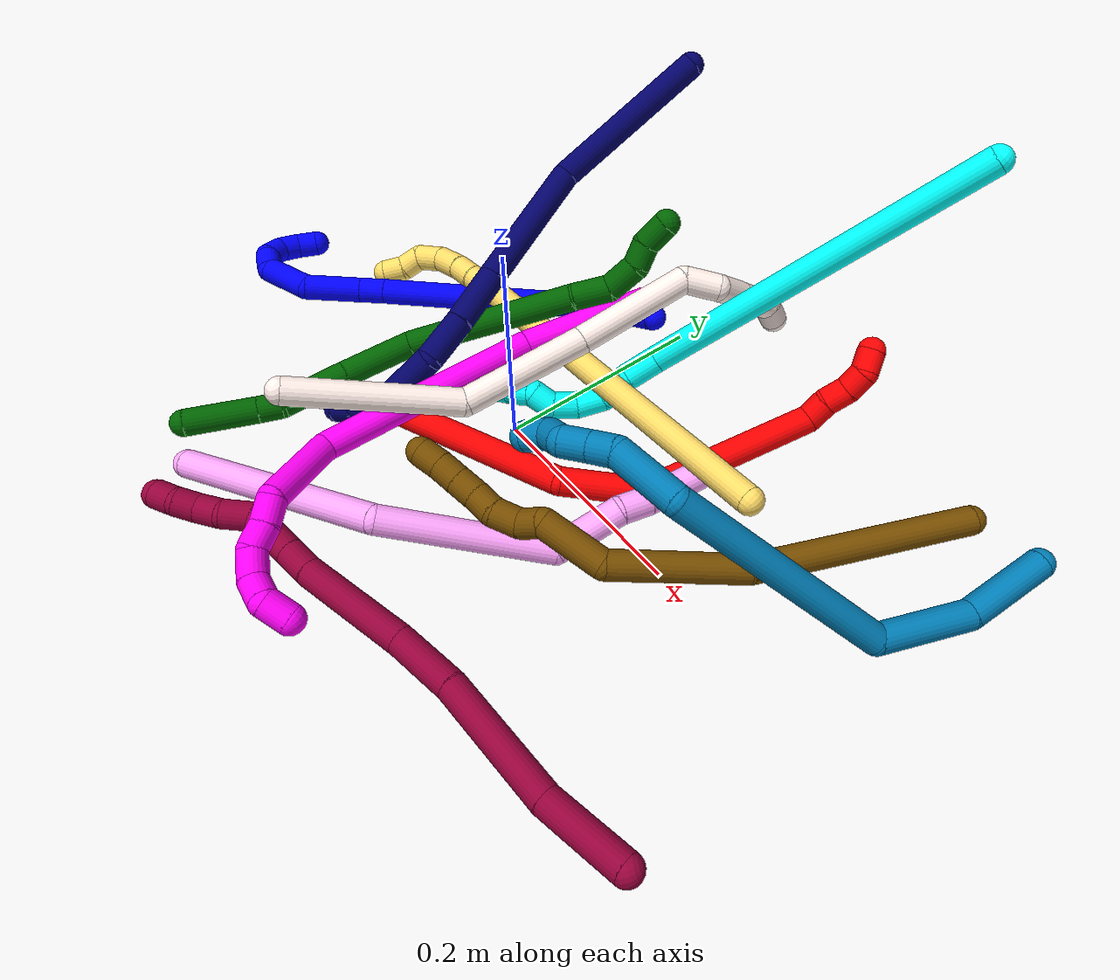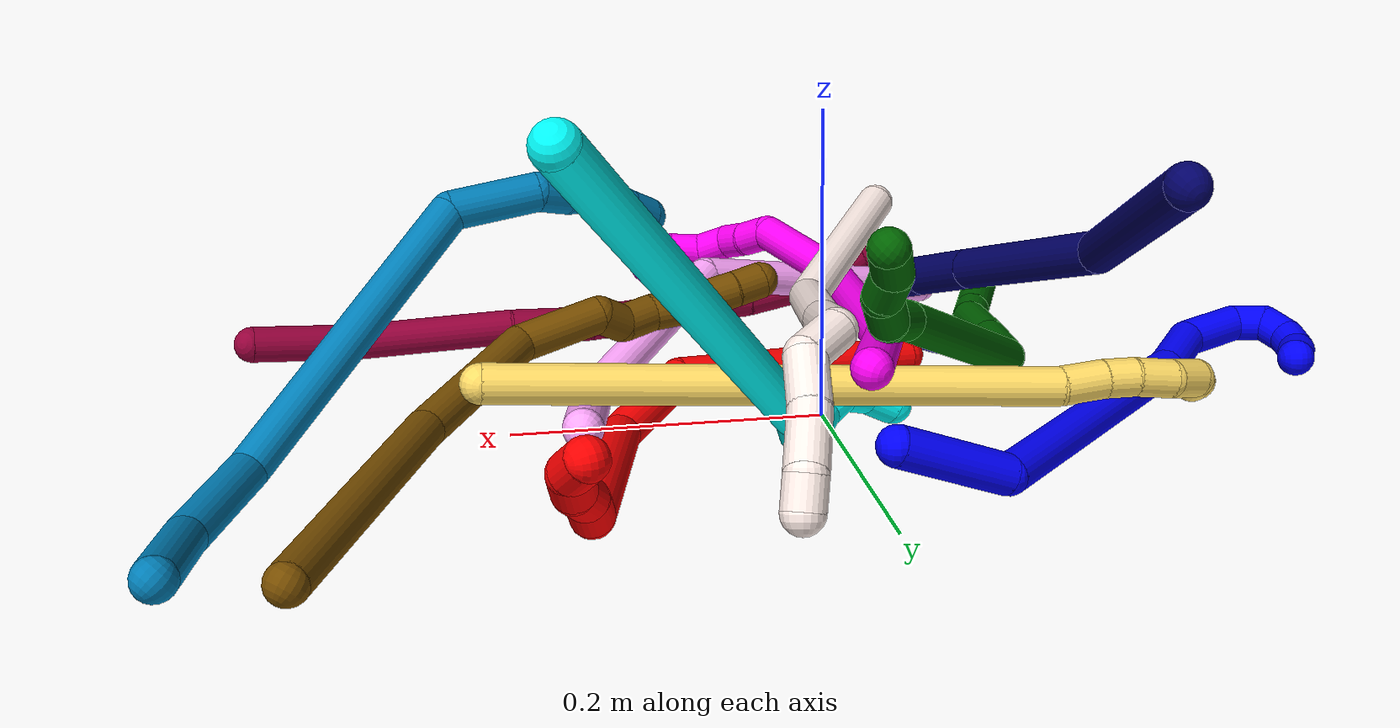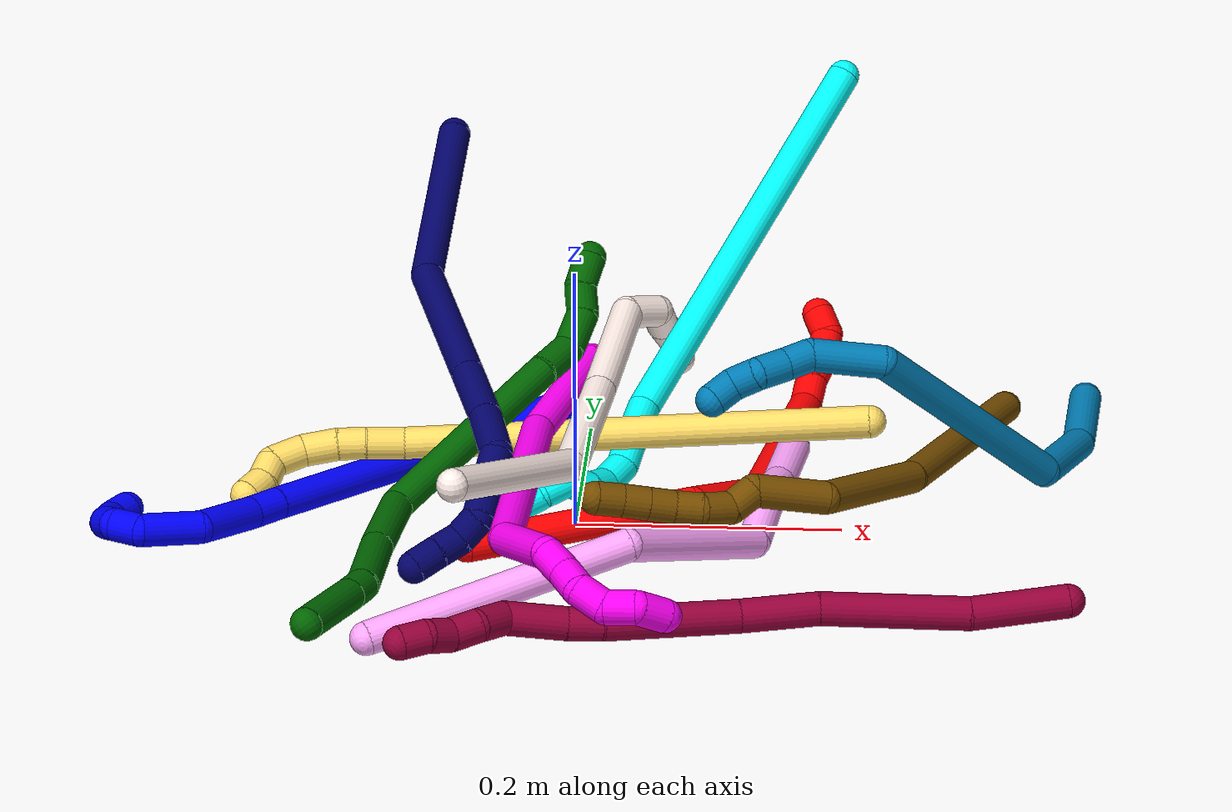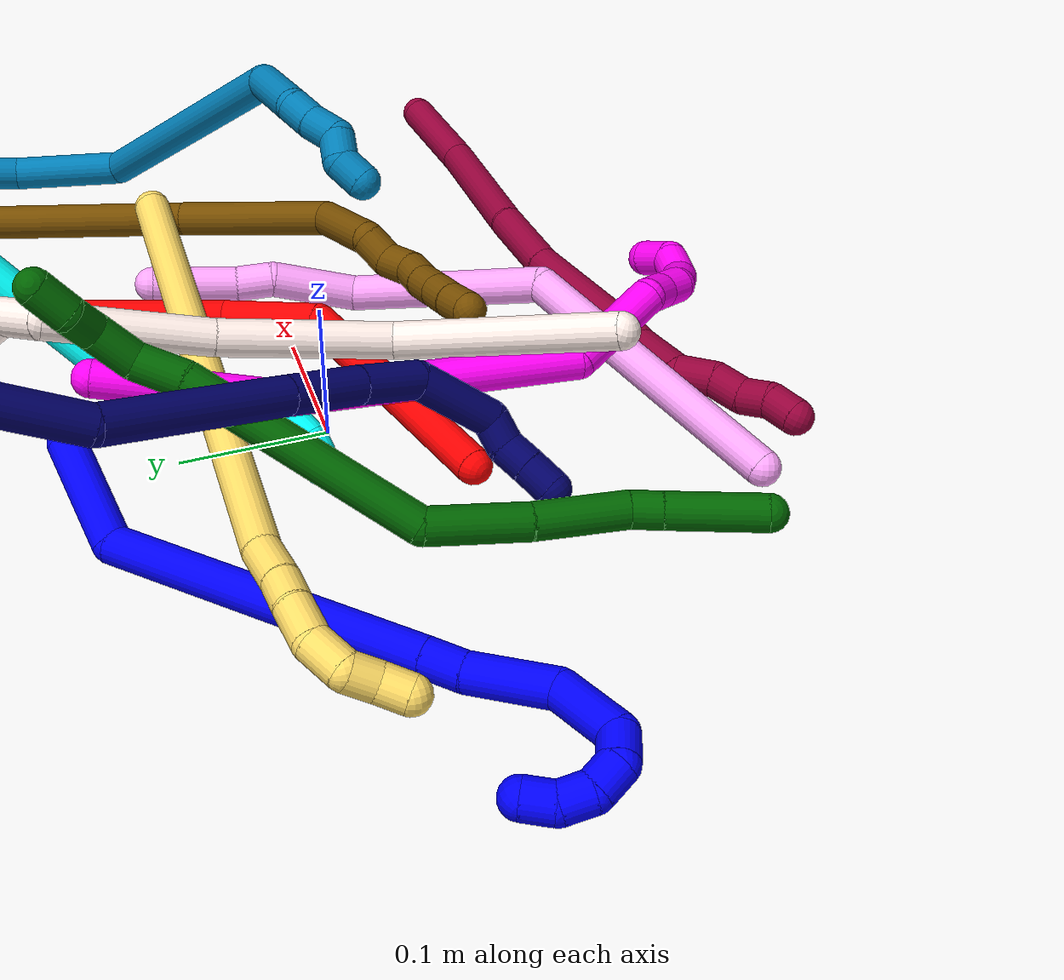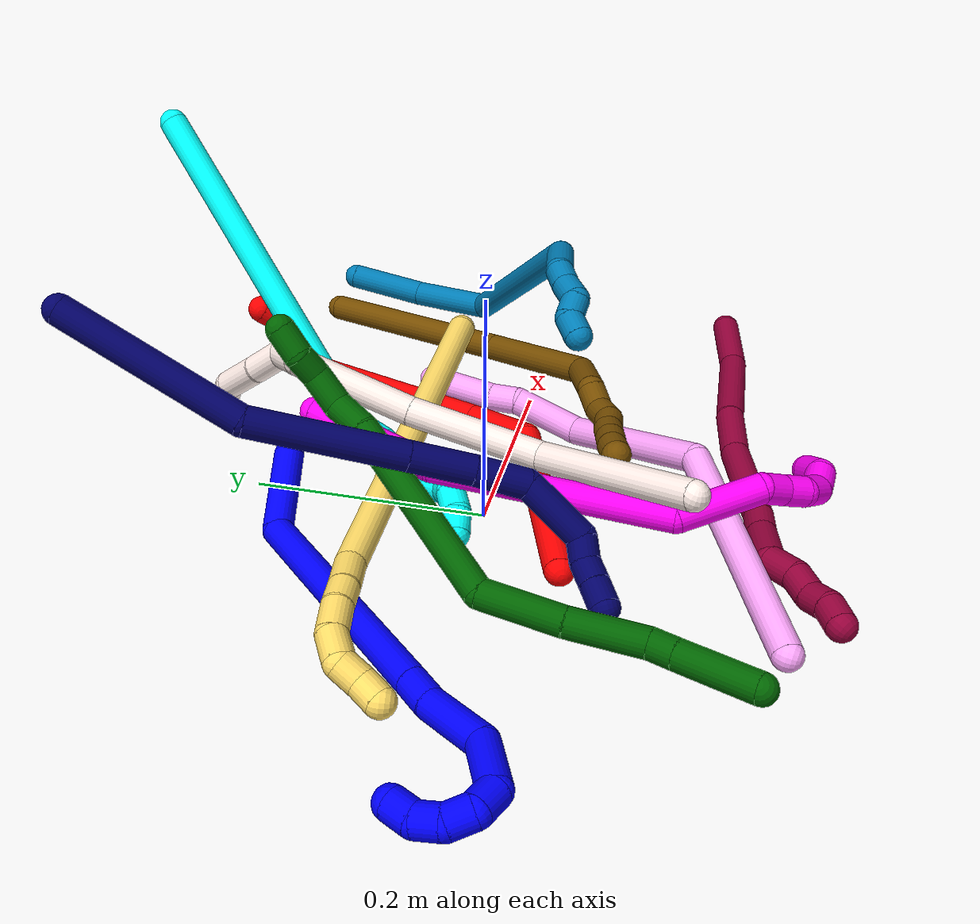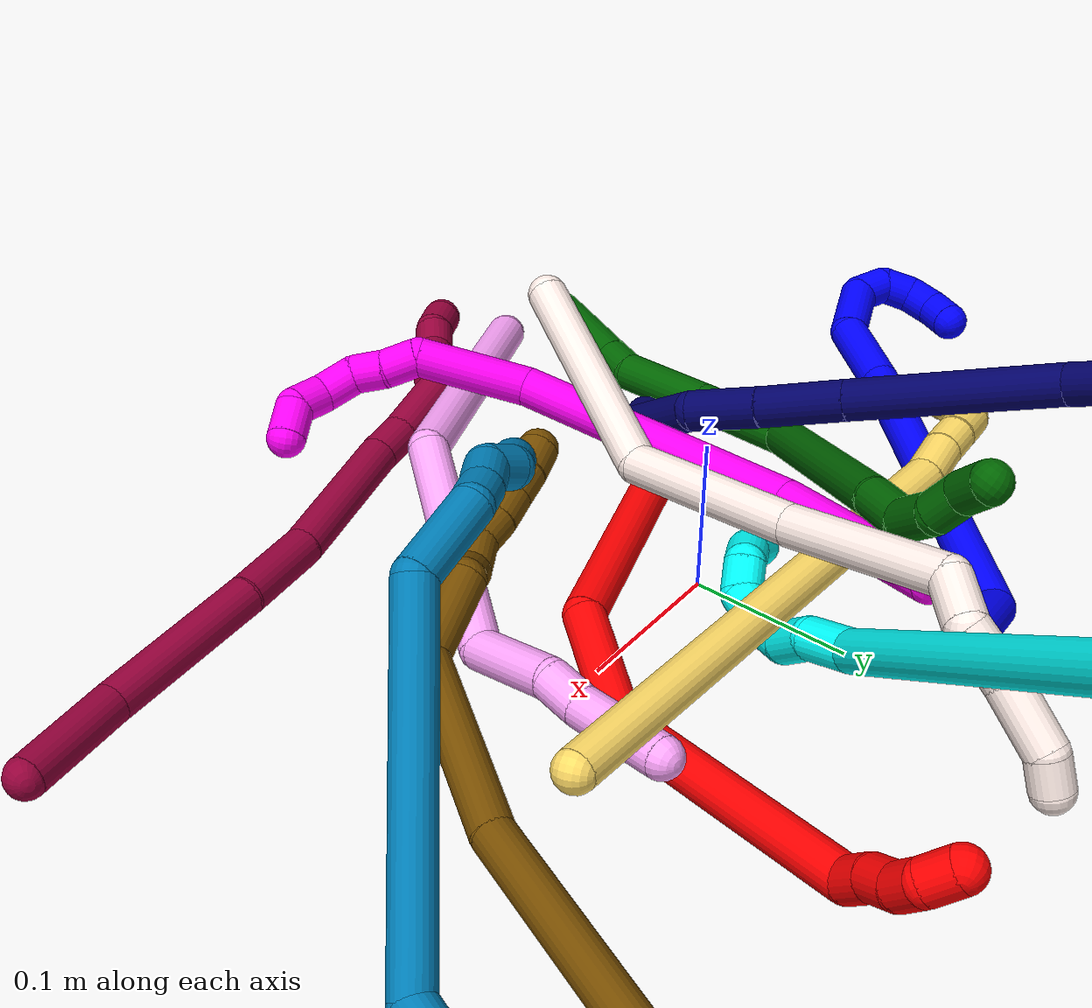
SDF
<sdf version="1.7">
 <world name="default">
  <plugin name="TubeGeneratorPlugin" filename="libtube_generator_plugin.so"/>
  <model name="photoneo_s_sensor">
   <static>1</static>
   <pose>0 0 2 1.57079 1.57079 3.14159</pose>
   <link name="link">
    <inertial><mass>0.1</mass></inertial>
    <sensor name="sensor" type="depth">
     <update_rate>30</update_rate>
     <camera>
      <horizontal_fov>1.22</horizontal_fov>
      <image><width>1920</width><height>1200</height><format>B8G8R8</format></image>
      <clip><near>0.1</near><far>4</far></clip>
      <depth_camera><output>points</output></depth_camera>
     </camera>
     <plugin name="camera_plugin" filename="libgazebo_ros_depth_camera.so">
      <baseline>0.2</baseline>
      <alwaysOn>1</alwaysOn>
      <updateRate>0.0</updateRate>
      <cameraName>camera_ir</cameraName>
      <imageTopicName>/camera/color/image_raw</imageTopicName>
      <cameraInfoTopicName>/camera/color/camera_info</cameraInfoTopicName>
      <depthImageTopicName>/camera/depth/image_raw</depthImageTopicName>
      <depthImageCameraInfoTopicName>/camera/depth/camera_info</depthImageCameraInfoTopicName>
      <pointCloudTopicName>/camera/depth/points</pointCloudTopicName>
      <frameName>fr_optical</frameName>
      <pointCloudCutoff>0.1</pointCloudCutoff>
      <pointCloudCutoffMax>2.0</pointCloudCutoffMax>
      <distortionK1>0</distortionK1>
      <distortionK2>0</distortionK2>
      <distortionK3>0</distortionK3>
      <distortionT1>0</distortionT1>
      <distortionT2>0</distortionT2>
      <CxPrime>0</CxPrime>
      <Cx>0</Cx>
      <Cy>0</Cy>
      <focalLength>0</focalLength>
      <hackBaseline>0</hackBaseline>
     </plugin>
    </sensor>
   </link>
  </model>
  <gravity>0 0 -9.8</gravity>
  <magnetic_field>6e-06 2.3e-05 -4.2e-05</magnetic_field>
  <atmosphere type="adiabatic"/>
  <physics name="default_physics" default="0" type="ode">
   <max_step_size>0.003</max_step_size>
   <real_time_factor>1</real_time_factor>
   <real_time_update_rate>1000</real_time_update_rate>
   <max_contacts>10000</max_contacts>
   <ode>
    <solver>
     <type>quick</type>
     <iters>100</iters>
     <sor>1.3</sor>
     <use_dynamic_moi_rescaling>0</use_dynamic_moi_rescaling>
    </solver>
    <constraints>
     <contact_max_correcting_vel>0</contact_max_correcting_vel>
     <contact_surface_layer>0.001</contact_surface_layer>
     <cfm>0</cfm>
     <erp>0.2</erp>
    </constraints>
   </ode>
  </physics>
  <scene><ambient>0.4 0.4 0.4 1</ambient><background>0.7 0.7 0.7 1</background><shadows>0</shadows></scene>
  <audio><device>default</device></audio>
  <spherical_coordinates>
   <surface_model>EARTH_WGS84</surface_model>
   <latitude_deg>0</latitude_deg>
   <longitude_deg>0</longitude_deg>
   <elevation>0</elevation>
   <heading_deg>0</heading_deg>
  </spherical_coordinates>
  <model name="bin">
   <static>1</static>
   <link name="bottom">
    <collision name="collision-bottom">
     <pose>0 0 -0.01 0 -0 0</pose>
     <geometry><box><size>0.8 0.6 0.02</size></box></geometry>
     <surface>
      <friction><ode><mu>100</mu><mu2>100</mu2></ode></friction>
      <contact><collide_bitmask>65535</collide_bitmask></contact>
     </surface>
    </collision>
   </link>
   <link name="west_wall">
    <collision name="collision-west_wall">
     <pose>-0.41 0 0.1 0 -0 0</pose>
     <geometry><box><size>0.02 0.6 0.2</size></box></geometry>
     <surface>
      <friction><ode><mu>100</mu><mu2>100</mu2></ode></friction>
      <contact><collide_bitmask>65535</collide_bitmask></contact>
     </surface>
    </collision>
   </link>
   <link name="east_wall">
    <collision name="collision-east_wall">
     <pose>0.41 0 0.1 0 -0 0</pose>
     <geometry><box><size>0.02 0.6 0.2</size></box></geometry>
     <surface>
      <friction><ode><mu>100</mu><mu2>100</mu2></ode></friction>
      <contact><collide_bitmask>65535</collide_bitmask></contact>
     </surface>
    </collision>
   </link>
   <link name="south_wall">
    <collision name="collision-south_wall">
     <pose>0 -0.31 0.1 0 -0 0</pose>
     <geometry><box><size>0.8 0.02 0.2</size></box></geometry>
     <surface>
      <friction><ode><mu>100</mu><mu2>100</mu2></ode></friction>
      <contact><collide_bitmask>65535</collide_bitmask></contact>
     </surface>
    </collision>
   </link>
   <link name="north_wall">
    <collision name="collision-north_wall">
     <pose>0 0.31 0.1 0 -0 0</pose>
     <geometry><box><size>0.8 0.02 0.2</size></box></geometry>
     <surface>
      <friction><ode><mu>100</mu><mu2>100</mu2></ode></friction>
      <contact><collide_bitmask>65535</collide_bitmask></contact>
     </surface>
    </collision>
   </link>
  </model>
  <model name="1">
   <static>0</static>
   <link name="1">
    <collision name="collision-cylinder-e_1_1_4">
     <pose>-0.012231 0.012747 0.034111 -0.357617 -0.324036 0.059067</pose>
     <geometry><cylinder><radius>0.0125</radius><length>0.076828</length></cylinder></geometry>
     <surface>
      <friction><ode><mu>1.16</mu><mu2>1.16</mu2><slip1>0</slip1><slip2>0</slip2></ode></friction>
      <contact><ode><kp>1e+06</kp><kd>1</kd><max_vel>0</max_vel><min_depth>0.001</min_depth></ode></contact>
     </surface>
    </collision>
    <visual name="visual-cylinder-e_1_1_4">
     <pose>-0.012231 0.012747 0.034111 -0.357617 -0.324036 0.059067</pose>
     <geometry><cylinder><radius>0.0125</radius><length>0.076828</length></cylinder></geometry>
     <material><ambient>0 0 1 1</ambient></material>
    </visual>
    <collision name="collision-cylinder-e_2_4_5">
     <pose>-0.104946 0.010531 0.137583 0.212469 -0.848231 -0.096222</pose>
     <geometry><cylinder><radius>0.0125</radius><length>0.214593</length></cylinder></geometry>
     <surface>
      <friction><ode><mu>1.16</mu><mu2>1.16</mu2><slip1>0</slip1><slip2>0</slip2></ode></friction>
      <contact><ode><kp>1e+06</kp><kd>1</kd><max_vel>0</max_vel><min_depth>0.001</min_depth></ode></contact>
     </surface>
    </collision>
    <visual name="visual-cylinder-e_2_4_5">
     <pose>-0.104946 0.010531 0.137583 0.212469 -0.848231 -0.096222</pose>
     <geometry><cylinder><radius>0.0125</radius><length>0.214593</length></cylinder></geometry>
     <material><ambient>0 0 1 1</ambient></material>
    </visual>
    <collision name="collision-cylinder-e_3_5_6">
     <pose>-0.195024 -0.00589 0.215123 0.176338 -0.857061 -0.080724</pose>
     <geometry><cylinder><radius>0.0125</radius><length>0.025381</length></cylinder></geometry>
     <surface>
      <friction><ode><mu>1.16</mu><mu2>1.16</mu2><slip1>0</slip1><slip2>0</slip2></ode></friction>
      <contact><ode><kp>1e+06</kp><kd>1</kd><max_vel>0</max_vel><min_depth>0.001</min_depth></ode></contact>
     </surface>
    </collision>
    <visual name="visual-cylinder-e_3_5_6">
     <pose>-0.195024 -0.00589 0.215123 0.176338 -0.857061 -0.080724</pose>
     <geometry><cylinder><radius>0.0125</radius><length>0.025381</length></cylinder></geometry>
     <material><ambient>0 0 1 1</ambient></material>
    </visual>
    <collision name="collision-cylinder-e_4_6_7">
     <pose>-0.226775 -0.014229 0.238249 0.431494 -0.932027 -0.219569</pose>
     <geometry><cylinder><radius>0.0125</radius><length>0.055199</length></cylinder></geometry>
     <surface>
      <friction><ode><mu>1.16</mu><mu2>1.16</mu2><slip1>0</slip1><slip2>0</slip2></ode></friction>
      <contact><ode><kp>1e+06</kp><kd>1</kd><max_vel>0</max_vel><min_depth>0.001</min_depth></ode></contact>
     </surface>
    </collision>
    <visual name="visual-cylinder-e_4_6_7">
     <pose>-0.226775 -0.014229 0.238249 0.431494 -0.932027 -0.219569</pose>
     <geometry><cylinder><radius>0.0125</radius><length>0.055199</length></cylinder></geometry>
     <material><ambient>0 0 1 1</ambient></material>
    </visual>
    <collision name="collision-cylinder-e_5_7_8">
     <pose>-0.258738 -0.024387 0.273993 0.156212 -0.435857 -0.034659</pose>
     <geometry><cylinder><radius>0.0125</radius><length>0.04645</length></cylinder></geometry>
     <surface>
      <friction><ode><mu>1.16</mu><mu2>1.16</mu2><slip1>0</slip1><slip2>0</slip2></ode></friction>
      <contact><ode><kp>1e+06</kp><kd>1</kd><max_vel>0</max_vel><min_depth>0.001</min_depth></ode></contact>
     </surface>
    </collision>
    <visual name="visual-cylinder-e_5_7_8">
     <pose>-0.258738 -0.024387 0.273993 0.156212 -0.435857 -0.034659</pose>
     <geometry><cylinder><radius>0.0125</radius><length>0.04645</length></cylinder></geometry>
     <material><ambient>0 0 1 1</ambient></material>
    </visual>
    <collision name="collision-cylinder-e_6_8_9">
     <pose>-0.265271 -0.027162 0.305038 -0.048759 0.308704 -0.007588</pose>
     <geometry><cylinder><radius>0.0125</radius><length>0.021538</length></cylinder></geometry>
     <surface>
      <friction><ode><mu>1.16</mu><mu2>1.16</mu2><slip1>0</slip1><slip2>0</slip2></ode></friction>
      <contact><ode><kp>1e+06</kp><kd>1</kd><max_vel>0</max_vel><min_depth>0.001</min_depth></ode></contact>
     </surface>
    </collision>
    <visual name="visual-cylinder-e_6_8_9">
     <pose>-0.265271 -0.027162 0.305038 -0.048759 0.308704 -0.007588</pose>
     <geometry><cylinder><radius>0.0125</radius><length>0.021538</length></cylinder></geometry>
     <material><ambient>0 0 1 1</ambient></material>
    </visual>
    <collision name="collision-cylinder-e_7_9_10">
     <pose>-0.254554 -0.022153 0.320214 -0.741012 0.839569 -0.343325</pose>
     <geometry><cylinder><radius>0.0125</radius><length>0.020005</length></cylinder></geometry>
     <surface>
      <friction><ode><mu>1.16</mu><mu2>1.16</mu2><slip1>0</slip1><slip2>0</slip2></ode></friction>
      <contact><ode><kp>1e+06</kp><kd>1</kd><max_vel>0</max_vel><min_depth>0.001</min_depth></ode></contact>
     </surface>
    </collision>
    <visual name="visual-cylinder-e_7_9_10">
     <pose>-0.254554 -0.022153 0.320214 -0.741012 0.839569 -0.343325</pose>
     <geometry><cylinder><radius>0.0125</radius><length>0.020005</length></cylinder></geometry>
     <material><ambient>0 0 1 1</ambient></material>
    </visual>
    <collision name="collision-cylinder-e_8_10_11">
     <pose>-0.237898 -0.013744 0.325119 -1.57674 1.17023 -1.1757</pose>
     <geometry><cylinder><radius>0.0125</radius><length>0.020005</length></cylinder></geometry>
     <surface>
      <friction><ode><mu>1.16</mu><mu2>1.16</mu2><slip1>0</slip1><slip2>0</slip2></ode></friction>
      <contact><ode><kp>1e+06</kp><kd>1</kd><max_vel>0</max_vel><min_depth>0.001</min_depth></ode></contact>
     </surface>
    </collision>
    <visual name="visual-cylinder-e_8_10_11">
     <pose>-0.237898 -0.013744 0.325119 -1.57674 1.17023 -1.1757</pose>
     <geometry><cylinder><radius>0.0125</radius><length>0.020005</length></cylinder></geometry>
     <material><ambient>0 0 1 1</ambient></material>
    </visual>
    <collision name="collision-cylinder-e_9_11_2">
     <pose>-0.219618 -0.008408 0.321134 -2.79403 1.13587 -2.60462</pose>
     <geometry><cylinder><radius>0.0125</radius><length>0.02</length></cylinder></geometry>
     <surface>
      <friction><ode><mu>1.16</mu><mu2>1.16</mu2><slip1>0</slip1><slip2>0</slip2></ode></friction>
      <contact><ode><kp>1e+06</kp><kd>1</kd><max_vel>0</max_vel><min_depth>0.001</min_depth></ode></contact>
     </surface>
    </collision>
    <visual name="visual-cylinder-e_9_11_2">
     <pose>-0.219618 -0.008408 0.321134 -2.79403 1.13587 -2.60462</pose>
     <geometry><cylinder><radius>0.0125</radius><length>0.02</length></cylinder></geometry>
     <material><ambient>0 0 1 1</ambient></material>
    </visual>
    <collision name="collision-sphere-2">
     <pose>-0.210549 -0.006973 0.317173 0 -0 0</pose>
     <geometry><sphere><radius>0.0125</radius></sphere></geometry>
     <surface>
      <friction><ode><mu>1.16</mu><mu2>1.16</mu2><slip1>0</slip1><slip2>0</slip2></ode></friction>
      <contact><ode><kp>1e+06</kp><kd>1</kd><max_vel>0</max_vel><min_depth>0.001</min_depth></ode></contact>
     </surface>
    </collision>
    <visual name="visual-sphere-2">
     <pose>-0.210549 -0.006973 0.317173 0 -0 0</pose>
     <geometry><sphere><radius>0.0125</radius></sphere></geometry>
     <material><ambient>0 0 1 1</ambient></material>
    </visual>
    <collision name="collision-sphere-11">
     <pose>-0.228687 -0.009843 0.325096 0 -0 0</pose>
     <geometry><sphere><radius>0.0125</radius></sphere></geometry>
     <surface>
      <friction><ode><mu>1.16</mu><mu2>1.16</mu2><slip1>0</slip1><slip2>0</slip2></ode></friction>
      <contact><ode><kp>1e+06</kp><kd>1</kd><max_vel>0</max_vel><min_depth>0.001</min_depth></ode></contact>
     </surface>
    </collision>
    <visual name="visual-sphere-11">
     <pose>-0.228687 -0.009843 0.325096 0 -0 0</pose>
     <geometry><sphere><radius>0.0125</radius></sphere></geometry>
     <material><ambient>0 0 1 1</ambient></material>
    </visual>
    <collision name="collision-sphere-10">
     <pose>-0.247109 -0.017644 0.325142 0 -0 0</pose>
     <geometry><sphere><radius>0.0125</radius></sphere></geometry>
     <surface>
      <friction><ode><mu>1.16</mu><mu2>1.16</mu2><slip1>0</slip1><slip2>0</slip2></ode></friction>
      <contact><ode><kp>1e+06</kp><kd>1</kd><max_vel>0</max_vel><min_depth>0.001</min_depth></ode></contact>
     </surface>
    </collision>
    <visual name="visual-sphere-10">
     <pose>-0.247109 -0.017644 0.325142 0 -0 0</pose>
     <geometry><sphere><radius>0.0125</radius></sphere></geometry>
     <material><ambient>0 0 1 1</ambient></material>
    </visual>
    <collision name="collision-sphere-9">
     <pose>-0.262 -0.026662 0.315286 0 -0 0</pose>
     <geometry><sphere><radius>0.0125</radius></sphere></geometry>
     <surface>
      <friction><ode><mu>1.16</mu><mu2>1.16</mu2><slip1>0</slip1><slip2>0</slip2></ode></friction>
      <contact><ode><kp>1e+06</kp><kd>1</kd><max_vel>0</max_vel><min_depth>0.001</min_depth></ode></contact>
     </surface>
    </collision>
    <visual name="visual-sphere-9">
     <pose>-0.262 -0.026662 0.315286 0 -0 0</pose>
     <geometry><sphere><radius>0.0125</radius></sphere></geometry>
     <material><ambient>0 0 1 1</ambient></material>
    </visual>
    <collision name="collision-sphere-4">
     <pose>-0.024462 0.025494 0.068222 0 -0 0</pose>
     <geometry><sphere><radius>0.0125</radius></sphere></geometry>
     <surface>
      <friction><ode><mu>1.16</mu><mu2>1.16</mu2><slip1>0</slip1><slip2>0</slip2></ode></friction>
      <contact><ode><kp>1e+06</kp><kd>1</kd><max_vel>0</max_vel><min_depth>0.001</min_depth></ode></contact>
     </surface>
    </collision>
    <visual name="visual-sphere-4">
     <pose>-0.024462 0.025494 0.068222 0 -0 0</pose>
     <geometry><sphere><radius>0.0125</radius></sphere></geometry>
     <material><ambient>0 0 1 1</ambient></material>
    </visual>
    <collision name="collision-sphere-1">
     <geometry><sphere><radius>0.0125</radius></sphere></geometry>
     <surface>
      <friction><ode><mu>1.16</mu><mu2>1.16</mu2><slip1>0</slip1><slip2>0</slip2></ode></friction>
      <contact><ode><kp>1e+06</kp><kd>1</kd><max_vel>0</max_vel><min_depth>0.001</min_depth></ode></contact>
     </surface>
    </collision>
    <visual name="visual-sphere-1">
     <geometry><sphere><radius>0.0125</radius></sphere></geometry>
     <material><ambient>0 0 1 1</ambient></material>
    </visual>
    <collision name="collision-sphere-8">
     <pose>-0.268543 -0.027662 0.294791 0 -0 0</pose>
     <geometry><sphere><radius>0.0125</radius></sphere></geometry>
     <surface>
      <friction><ode><mu>1.16</mu><mu2>1.16</mu2><slip1>0</slip1><slip2>0</slip2></ode></friction>
      <contact><ode><kp>1e+06</kp><kd>1</kd><max_vel>0</max_vel><min_depth>0.001</min_depth></ode></contact>
     </surface>
    </collision>
    <visual name="visual-sphere-8">
     <pose>-0.268543 -0.027662 0.294791 0 -0 0</pose>
     <geometry><sphere><radius>0.0125</radius></sphere></geometry>
     <material><ambient>0 0 1 1</ambient></material>
    </visual>
    <collision name="collision-sphere-5">
     <pose>-0.185431 -0.004432 0.206944 0 -0 0</pose>
     <geometry><sphere><radius>0.0125</radius></sphere></geometry>
     <surface>
      <friction><ode><mu>1.16</mu><mu2>1.16</mu2><slip1>0</slip1><slip2>0</slip2></ode></friction>
      <contact><ode><kp>1e+06</kp><kd>1</kd><max_vel>0</max_vel><min_depth>0.001</min_depth></ode></contact>
     </surface>
    </collision>
    <visual name="visual-sphere-5">
     <pose>-0.185431 -0.004432 0.206944 0 -0 0</pose>
     <geometry><sphere><radius>0.0125</radius></sphere></geometry>
     <material><ambient>0 0 1 1</ambient></material>
    </visual>
    <collision name="collision-sphere-6">
     <pose>-0.204617 -0.007347 0.223302 0 -0 0</pose>
     <geometry><sphere><radius>0.0125</radius></sphere></geometry>
     <surface>
      <friction><ode><mu>1.16</mu><mu2>1.16</mu2><slip1>0</slip1><slip2>0</slip2></ode></friction>
      <contact><ode><kp>1e+06</kp><kd>1</kd><max_vel>0</max_vel><min_depth>0.001</min_depth></ode></contact>
     </surface>
    </collision>
    <visual name="visual-sphere-6">
     <pose>-0.204617 -0.007347 0.223302 0 -0 0</pose>
     <geometry><sphere><radius>0.0125</radius></sphere></geometry>
     <material><ambient>0 0 1 1</ambient></material>
    </visual>
    <collision name="collision-sphere-7">
     <pose>-0.248933 -0.021111 0.253196 0 -0 0</pose>
     <geometry><sphere><radius>0.0125</radius></sphere></geometry>
     <surface>
      <friction><ode><mu>1.16</mu><mu2>1.16</mu2><slip1>0</slip1><slip2>0</slip2></ode></friction>
      <contact><ode><kp>1e+06</kp><kd>1</kd><max_vel>0</max_vel><min_depth>0.001</min_depth></ode></contact>
     </surface>
    </collision>
    <visual name="visual-sphere-7">
     <pose>-0.248933 -0.021111 0.253196 0 -0 0</pose>
     <geometry><sphere><radius>0.0125</radius></sphere></geometry>
     <material><ambient>0 0 1 1</ambient></material>
    </visual>
    <inertial>
     <pose>-0.145808 -0.0006 0.178772 0 -0 0</pose>
     <mass>0.5</mass>
     <inertia>
      <ixx>0.000538</ixx>
      <ixy>0</ixy>
      <ixz>0</ixz>
      <iyy>0.000839</iyy>
      <iyz>0</iyz>
      <izz>0.000783</izz>
     </inertia>
    </inertial>
   </link>
   <pose>-0.006132 0.167715 0.039268 -1.53782 -0.207533 1.4989</pose>
  </model>
  <model name="2">
   <static>0</static>
   <link name="2">
    <collision name="collision-cylinder-e_1_1_4">
     <pose>0.005272 -0.011925 -0.087458 3.00608 0.059652 0.828425</pose>
     <geometry><cylinder><radius>0.0125</radius><length>0.176849</length></cylinder></geometry>
     <surface>
      <friction><ode><mu>1.16</mu><mu2>1.16</mu2><slip1>0</slip1><slip2>0</slip2></ode></friction>
      <contact><ode><kp>1e+06</kp><kd>1</kd><max_vel>0</max_vel><min_depth>0.001</min_depth></ode></contact>
     </surface>
    </collision>
    <visual name="visual-cylinder-e_1_1_4">
     <pose>0.005272 -0.011925 -0.087458 3.00608 0.059652 0.828425</pose>
     <geometry><cylinder><radius>0.0125</radius><length>0.176849</length></cylinder></geometry>
     <material><ambient>1 0 0 1</ambient></material>
    </visual>
    <collision name="collision-cylinder-e_2_4_5">
     <pose>0.017748 -0.006672 -0.207553 -2.65711 0.192927 -0.746506</pose>
     <geometry><cylinder><radius>0.0125</radius><length>0.075157</length></cylinder></geometry>
     <surface>
      <friction><ode><mu>1.16</mu><mu2>1.16</mu2><slip1>0</slip1><slip2>0</slip2></ode></friction>
      <contact><ode><kp>1e+06</kp><kd>1</kd><max_vel>0</max_vel><min_depth>0.001</min_depth></ode></contact>
     </surface>
    </collision>
    <visual name="visual-cylinder-e_2_4_5">
     <pose>0.017748 -0.006672 -0.207553 -2.65711 0.192927 -0.746506</pose>
     <geometry><cylinder><radius>0.0125</radius><length>0.075157</length></cylinder></geometry>
     <material><ambient>1 0 0 1</ambient></material>
    </visual>
    <collision name="collision-cylinder-e_3_5_6">
     <pose>0.074787 0.055445 -0.286913 -2.37565 0.655372 -1.40178</pose>
     <geometry><cylinder><radius>0.0125</radius><length>0.163536</length></cylinder></geometry>
     <surface>
      <friction><ode><mu>1.16</mu><mu2>1.16</mu2><slip1>0</slip1><slip2>0</slip2></ode></friction>
      <contact><ode><kp>1e+06</kp><kd>1</kd><max_vel>0</max_vel><min_depth>0.001</min_depth></ode></contact>
     </surface>
    </collision>
    <visual name="visual-cylinder-e_3_5_6">
     <pose>0.074787 0.055445 -0.286913 -2.37565 0.655372 -1.40178</pose>
     <geometry><cylinder><radius>0.0125</radius><length>0.163536</length></cylinder></geometry>
     <material><ambient>1 0 0 1</ambient></material>
    </visual>
    <collision name="collision-cylinder-e_4_6_7">
     <pose>0.134712 0.099808 -0.338112 3.01357 1.15025 2.94447</pose>
     <geometry><cylinder><radius>0.0125</radius><length>0.022109</length></cylinder></geometry>
     <surface>
      <friction><ode><mu>1.16</mu><mu2>1.16</mu2><slip1>0</slip1><slip2>0</slip2></ode></friction>
      <contact><ode><kp>1e+06</kp><kd>1</kd><max_vel>0</max_vel><min_depth>0.001</min_depth></ode></contact>
     </surface>
    </collision>
    <visual name="visual-cylinder-e_4_6_7">
     <pose>0.134712 0.099808 -0.338112 3.01357 1.15025 2.94447</pose>
     <geometry><cylinder><radius>0.0125</radius><length>0.022109</length></cylinder></geometry>
     <material><ambient>1 0 0 1</ambient></material>
    </visual>
    <collision name="collision-cylinder-e_5_7_8">
     <pose>0.153432 0.100011 -0.349155 -3.02353 0.916863 -2.90321</pose>
     <geometry><cylinder><radius>0.0125</radius><length>0.021743</length></cylinder></geometry>
     <surface>
      <friction><ode><mu>1.16</mu><mu2>1.16</mu2><slip1>0</slip1><slip2>0</slip2></ode></friction>
      <contact><ode><kp>1e+06</kp><kd>1</kd><max_vel>0</max_vel><min_depth>0.001</min_depth></ode></contact>
     </surface>
    </collision>
    <visual name="visual-cylinder-e_5_7_8">
     <pose>0.153432 0.100011 -0.349155 -3.02353 0.916863 -2.90321</pose>
     <geometry><cylinder><radius>0.0125</radius><length>0.021743</length></cylinder></geometry>
     <material><ambient>1 0 0 1</ambient></material>
    </visual>
    <collision name="collision-cylinder-e_6_8_9">
     <pose>0.171592 0.09986 -0.359514 2.90105 1.18199 2.78519</pose>
     <geometry><cylinder><radius>0.0125</radius><length>0.0206</length></cylinder></geometry>
     <surface>
      <friction><ode><mu>1.16</mu><mu2>1.16</mu2><slip1>0</slip1><slip2>0</slip2></ode></friction>
      <contact><ode><kp>1e+06</kp><kd>1</kd><max_vel>0</max_vel><min_depth>0.001</min_depth></ode></contact>
     </surface>
    </collision>
    <visual name="visual-cylinder-e_6_8_9">
     <pose>0.171592 0.09986 -0.359514 2.90105 1.18199 2.78519</pose>
     <geometry><cylinder><radius>0.0125</radius><length>0.0206</length></cylinder></geometry>
     <material><ambient>1 0 0 1</ambient></material>
    </visual>
    <collision name="collision-cylinder-e_7_9_2">
     <pose>0.190834 0.101162 -0.362426 -1.19504 1.32856 -0.979119</pose>
     <geometry><cylinder><radius>0.0125</radius><length>0.020006</length></cylinder></geometry>
     <surface>
      <friction><ode><mu>1.16</mu><mu2>1.16</mu2><slip1>0</slip1><slip2>0</slip2></ode></friction>
      <contact><ode><kp>1e+06</kp><kd>1</kd><max_vel>0</max_vel><min_depth>0.001</min_depth></ode></contact>
     </surface>
    </collision>
    <visual name="visual-cylinder-e_7_9_2">
     <pose>0.190834 0.101162 -0.362426 -1.19504 1.32856 -0.979119</pose>
     <geometry><cylinder><radius>0.0125</radius><length>0.020006</length></cylinder></geometry>
     <material><ambient>1 0 0 1</ambient></material>
    </visual>
    <collision name="collision-sphere-2">
     <pose>0.200545 0.103394 -0.361545 0 -0 0</pose>
     <geometry><sphere><radius>0.0125</radius></sphere></geometry>
     <surface>
      <friction><ode><mu>1.16</mu><mu2>1.16</mu2><slip1>0</slip1><slip2>0</slip2></ode></friction>
      <contact><ode><kp>1e+06</kp><kd>1</kd><max_vel>0</max_vel><min_depth>0.001</min_depth></ode></contact>
     </surface>
    </collision>
    <visual name="visual-sphere-2">
     <pose>0.200545 0.103394 -0.361545 0 -0 0</pose>
     <geometry><sphere><radius>0.0125</radius></sphere></geometry>
     <material><ambient>1 0 0 1</ambient></material>
    </visual>
    <collision name="collision-sphere-9">
     <pose>0.181123 0.09893 -0.363307 0 -0 0</pose>
     <geometry><sphere><radius>0.0125</radius></sphere></geometry>
     <surface>
      <friction><ode><mu>1.16</mu><mu2>1.16</mu2><slip1>0</slip1><slip2>0</slip2></ode></friction>
      <contact><ode><kp>1e+06</kp><kd>1</kd><max_vel>0</max_vel><min_depth>0.001</min_depth></ode></contact>
     </surface>
    </collision>
    <visual name="visual-sphere-9">
     <pose>0.181123 0.09893 -0.363307 0 -0 0</pose>
     <geometry><sphere><radius>0.0125</radius></sphere></geometry>
     <material><ambient>1 0 0 1</ambient></material>
    </visual>
    <collision name="collision-sphere-4">
     <pose>0.010543 -0.02385 -0.174916 0 -0 0</pose>
     <geometry><sphere><radius>0.0125</radius></sphere></geometry>
     <surface>
      <friction><ode><mu>1.16</mu><mu2>1.16</mu2><slip1>0</slip1><slip2>0</slip2></ode></friction>
      <contact><ode><kp>1e+06</kp><kd>1</kd><max_vel>0</max_vel><min_depth>0.001</min_depth></ode></contact>
     </surface>
    </collision>
    <visual name="visual-sphere-4">
     <pose>0.010543 -0.02385 -0.174916 0 -0 0</pose>
     <geometry><sphere><radius>0.0125</radius></sphere></geometry>
     <material><ambient>1 0 0 1</ambient></material>
    </visual>
    <collision name="collision-sphere-1">
     <geometry><sphere><radius>0.0125</radius></sphere></geometry>
     <surface>
      <friction><ode><mu>1.16</mu><mu2>1.16</mu2><slip1>0</slip1><slip2>0</slip2></ode></friction>
      <contact><ode><kp>1e+06</kp><kd>1</kd><max_vel>0</max_vel><min_depth>0.001</min_depth></ode></contact>
     </surface>
    </collision>
    <visual name="visual-sphere-1">
     <geometry><sphere><radius>0.0125</radius></sphere></geometry>
     <material><ambient>1 0 0 1</ambient></material>
    </visual>
    <collision name="collision-sphere-8">
     <pose>0.162061 0.10079 -0.355722 0 -0 0</pose>
     <geometry><sphere><radius>0.0125</radius></sphere></geometry>
     <surface>
      <friction><ode><mu>1.16</mu><mu2>1.16</mu2><slip1>0</slip1><slip2>0</slip2></ode></friction>
      <contact><ode><kp>1e+06</kp><kd>1</kd><max_vel>0</max_vel><min_depth>0.001</min_depth></ode></contact>
     </surface>
    </collision>
    <visual name="visual-sphere-8">
     <pose>0.162061 0.10079 -0.355722 0 -0 0</pose>
     <geometry><sphere><radius>0.0125</radius></sphere></geometry>
     <material><ambient>1 0 0 1</ambient></material>
    </visual>
    <collision name="collision-sphere-5">
     <pose>0.024953 0.010505 -0.24019 0 -0 0</pose>
     <geometry><sphere><radius>0.0125</radius></sphere></geometry>
     <surface>
      <friction><ode><mu>1.16</mu><mu2>1.16</mu2><slip1>0</slip1><slip2>0</slip2></ode></friction>
      <contact><ode><kp>1e+06</kp><kd>1</kd><max_vel>0</max_vel><min_depth>0.001</min_depth></ode></contact>
     </surface>
    </collision>
    <visual name="visual-sphere-5">
     <pose>0.024953 0.010505 -0.24019 0 -0 0</pose>
     <geometry><sphere><radius>0.0125</radius></sphere></geometry>
     <material><ambient>1 0 0 1</ambient></material>
    </visual>
    <collision name="collision-sphere-6">
     <pose>0.124621 0.100384 -0.333635 0 -0 0</pose>
     <geometry><sphere><radius>0.0125</radius></sphere></geometry>
     <surface>
      <friction><ode><mu>1.16</mu><mu2>1.16</mu2><slip1>0</slip1><slip2>0</slip2></ode></friction>
      <contact><ode><kp>1e+06</kp><kd>1</kd><max_vel>0</max_vel><min_depth>0.001</min_depth></ode></contact>
     </surface>
    </collision>
    <visual name="visual-sphere-6">
     <pose>0.124621 0.100384 -0.333635 0 -0 0</pose>
     <geometry><sphere><radius>0.0125</radius></sphere></geometry>
     <material><ambient>1 0 0 1</ambient></material>
    </visual>
    <collision name="collision-sphere-7">
     <pose>0.144803 0.099232 -0.342588 0 -0 0</pose>
     <geometry><sphere><radius>0.0125</radius></sphere></geometry>
     <surface>
      <friction><ode><mu>1.16</mu><mu2>1.16</mu2><slip1>0</slip1><slip2>0</slip2></ode></friction>
      <contact><ode><kp>1e+06</kp><kd>1</kd><max_vel>0</max_vel><min_depth>0.001</min_depth></ode></contact>
     </surface>
    </collision>
    <visual name="visual-sphere-7">
     <pose>0.144803 0.099232 -0.342588 0 -0 0</pose>
     <geometry><sphere><radius>0.0125</radius></sphere></geometry>
     <material><ambient>1 0 0 1</ambient></material>
    </visual>
    <inertial>
     <pose>0.056327 0.029838 -0.21542 0 -0 0</pose>
     <mass>0.5</mass>
     <inertia>
      <ixx>0.000435</ixx>
      <ixy>0</ixy>
      <ixz>0</ixz>
      <iyy>-0.000181</iyy>
      <iyz>0</iyz>
      <izz>-0.000454</izz>
     </inertia>
    </inertial>
   </link>
   <pose>-0.075734 -0.077548 0.012379 -1.48676 -0.864641 1.91791</pose>
  </model>
  <model name="3">
   <static>0</static>
   <link name="3">
    <collision name="collision-cylinder-e_1_1_4">
     <pose>-0.02589 -0.025272 -0.159868 2.98481 -0.158614 -1.58243</pose>
     <geometry><cylinder><radius>0.0125</radius><length>0.327821</length></cylinder></geometry>
     <surface>
      <friction><ode><mu>1.16</mu><mu2>1.16</mu2><slip1>0</slip1><slip2>0</slip2></ode></friction>
      <contact><ode><kp>1e+06</kp><kd>1</kd><max_vel>0</max_vel><min_depth>0.001</min_depth></ode></contact>
     </surface>
    </collision>
    <visual name="visual-cylinder-e_1_1_4">
     <pose>-0.02589 -0.025272 -0.159868 2.98481 -0.158614 -1.58243</pose>
     <geometry><cylinder><radius>0.0125</radius><length>0.327821</length></cylinder></geometry>
     <material><ambient>0.003922 1 0.996078 1</ambient></material>
    </visual>
    <collision name="collision-cylinder-e_2_4_5">
     <pose>-0.048814 -0.057627 -0.333875 2.67725 0.185368 0.749143</pose>
     <geometry><cylinder><radius>0.0125</radius><length>0.032179</length></cylinder></geometry>
     <surface>
      <friction><ode><mu>1.16</mu><mu2>1.16</mu2><slip1>0</slip1><slip2>0</slip2></ode></friction>
      <contact><ode><kp>1e+06</kp><kd>1</kd><max_vel>0</max_vel><min_depth>0.001</min_depth></ode></contact>
     </surface>
    </collision>
    <visual name="visual-cylinder-e_2_4_5">
     <pose>-0.048814 -0.057627 -0.333875 2.67725 0.185368 0.749143</pose>
     <geometry><cylinder><radius>0.0125</radius><length>0.032179</length></cylinder></geometry>
     <material><ambient>0.003922 1 0.996078 1</ambient></material>
    </visual>
    <collision name="collision-cylinder-e_3_5_6">
     <pose>-0.045384 -0.066039 -0.362107 3.04752 0.032787 0.670327</pose>
     <geometry><cylinder><radius>0.0125</radius><length>0.028327</length></cylinder></geometry>
     <surface>
      <friction><ode><mu>1.16</mu><mu2>1.16</mu2><slip1>0</slip1><slip2>0</slip2></ode></friction>
      <contact><ode><kp>1e+06</kp><kd>1</kd><max_vel>0</max_vel><min_depth>0.001</min_depth></ode></contact>
     </surface>
    </collision>
    <visual name="visual-cylinder-e_3_5_6">
     <pose>-0.045384 -0.066039 -0.362107 3.04752 0.032787 0.670327</pose>
     <geometry><cylinder><radius>0.0125</radius><length>0.028327</length></cylinder></geometry>
     <material><ambient>0.003922 1 0.996078 1</ambient></material>
    </visual>
    <collision name="collision-cylinder-e_4_6_7">
     <pose>-0.0458 -0.074827 -0.387075 2.54037 -0.066647 -0.214243</pose>
     <geometry><cylinder><radius>0.0125</radius><length>0.026431</length></cylinder></geometry>
     <surface>
      <friction><ode><mu>1.16</mu><mu2>1.16</mu2><slip1>0</slip1><slip2>0</slip2></ode></friction>
      <contact><ode><kp>1e+06</kp><kd>1</kd><max_vel>0</max_vel><min_depth>0.001</min_depth></ode></contact>
     </surface>
    </collision>
    <visual name="visual-cylinder-e_4_6_7">
     <pose>-0.0458 -0.074827 -0.387075 2.54037 -0.066647 -0.214243</pose>
     <geometry><cylinder><radius>0.0125</radius><length>0.026431</length></cylinder></geometry>
     <material><ambient>0.003922 1 0.996078 1</ambient></material>
    </visual>
    <collision name="collision-cylinder-e_5_7_8">
     <pose>-0.047016 -0.092401 -0.404244 2.12754 -0.028177 -0.05072</pose>
     <geometry><cylinder><radius>0.0125</radius><length>0.023838</length></cylinder></geometry>
     <surface>
      <friction><ode><mu>1.16</mu><mu2>1.16</mu2><slip1>0</slip1><slip2>0</slip2></ode></friction>
      <contact><ode><kp>1e+06</kp><kd>1</kd><max_vel>0</max_vel><min_depth>0.001</min_depth></ode></contact>
     </surface>
    </collision>
    <visual name="visual-cylinder-e_5_7_8">
     <pose>-0.047016 -0.092401 -0.404244 2.12754 -0.028177 -0.05072</pose>
     <geometry><cylinder><radius>0.0125</radius><length>0.023838</length></cylinder></geometry>
     <material><ambient>0.003922 1 0.996078 1</ambient></material>
    </visual>
    <collision name="collision-cylinder-e_6_8_9">
     <pose>-0.052483 -0.111023 -0.411833 1.72164 -0.537714 -0.620443</pose>
     <geometry><cylinder><radius>0.0125</radius><length>0.020037</length></cylinder></geometry>
     <surface>
      <friction><ode><mu>1.16</mu><mu2>1.16</mu2><slip1>0</slip1><slip2>0</slip2></ode></friction>
      <contact><ode><kp>1e+06</kp><kd>1</kd><max_vel>0</max_vel><min_depth>0.001</min_depth></ode></contact>
     </surface>
    </collision>
    <visual name="visual-cylinder-e_6_8_9">
     <pose>-0.052483 -0.111023 -0.411833 1.72164 -0.537714 -0.620443</pose>
     <geometry><cylinder><radius>0.0125</radius><length>0.020037</length></cylinder></geometry>
     <material><ambient>0.003922 1 0.996078 1</ambient></material>
    </visual>
    <collision name="collision-cylinder-e_7_9_10">
     <pose>-0.063997 -0.123491 -0.420688 2.65902 -0.64206 -1.86742</pose>
     <geometry><cylinder><radius>0.0125</radius><length>0.021319</length></cylinder></geometry>
     <surface>
      <friction><ode><mu>1.16</mu><mu2>1.16</mu2><slip1>0</slip1><slip2>0</slip2></ode></friction>
      <contact><ode><kp>1e+06</kp><kd>1</kd><max_vel>0</max_vel><min_depth>0.001</min_depth></ode></contact>
     </surface>
    </collision>
    <visual name="visual-cylinder-e_7_9_10">
     <pose>-0.063997 -0.123491 -0.420688 2.65902 -0.64206 -1.86742</pose>
     <geometry><cylinder><radius>0.0125</radius><length>0.021319</length></cylinder></geometry>
     <material><ambient>0.003922 1 0.996078 1</ambient></material>
    </visual>
    <collision name="collision-cylinder-e_8_10_2">
     <pose>-0.077819 -0.128351 -0.434909 3.00758 -0.836172 -2.84176</pose>
     <geometry><cylinder><radius>0.0125</radius><length>0.020048</length></cylinder></geometry>
     <surface>
      <friction><ode><mu>1.16</mu><mu2>1.16</mu2><slip1>0</slip1><slip2>0</slip2></ode></friction>
      <contact><ode><kp>1e+06</kp><kd>1</kd><max_vel>0</max_vel><min_depth>0.001</min_depth></ode></contact>
     </surface>
    </collision>
    <visual name="visual-cylinder-e_8_10_2">
     <pose>-0.077819 -0.128351 -0.434909 3.00758 -0.836172 -2.84176</pose>
     <geometry><cylinder><radius>0.0125</radius><length>0.020048</length></cylinder></geometry>
     <material><ambient>0.003922 1 0.996078 1</ambient></material>
    </visual>
    <collision name="collision-sphere-2">
     <pose>-0.085258 -0.129249 -0.441568 0 -0 0</pose>
     <geometry><sphere><radius>0.0125</radius></sphere></geometry>
     <surface>
      <friction><ode><mu>1.16</mu><mu2>1.16</mu2><slip1>0</slip1><slip2>0</slip2></ode></friction>
      <contact><ode><kp>1e+06</kp><kd>1</kd><max_vel>0</max_vel><min_depth>0.001</min_depth></ode></contact>
     </surface>
    </collision>
    <visual name="visual-sphere-2">
     <pose>-0.085258 -0.129249 -0.441568 0 -0 0</pose>
     <geometry><sphere><radius>0.0125</radius></sphere></geometry>
     <material><ambient>0.003922 1 0.996078 1</ambient></material>
    </visual>
    <collision name="collision-sphere-10">
     <pose>-0.070381 -0.127453 -0.42825 0 -0 0</pose>
     <geometry><sphere><radius>0.0125</radius></sphere></geometry>
     <surface>
      <friction><ode><mu>1.16</mu><mu2>1.16</mu2><slip1>0</slip1><slip2>0</slip2></ode></friction>
      <contact><ode><kp>1e+06</kp><kd>1</kd><max_vel>0</max_vel><min_depth>0.001</min_depth></ode></contact>
     </surface>
    </collision>
    <visual name="visual-sphere-10">
     <pose>-0.070381 -0.127453 -0.42825 0 -0 0</pose>
     <geometry><sphere><radius>0.0125</radius></sphere></geometry>
     <material><ambient>0.003922 1 0.996078 1</ambient></material>
    </visual>
    <collision name="collision-sphere-9">
     <pose>-0.057614 -0.11953 -0.413126 0 -0 0</pose>
     <geometry><sphere><radius>0.0125</radius></sphere></geometry>
     <surface>
      <friction><ode><mu>1.16</mu><mu2>1.16</mu2><slip1>0</slip1><slip2>0</slip2></ode></friction>
      <contact><ode><kp>1e+06</kp><kd>1</kd><max_vel>0</max_vel><min_depth>0.001</min_depth></ode></contact>
     </surface>
    </collision>
    <visual name="visual-sphere-9">
     <pose>-0.057614 -0.11953 -0.413126 0 -0 0</pose>
     <geometry><sphere><radius>0.0125</radius></sphere></geometry>
     <material><ambient>0.003922 1 0.996078 1</ambient></material>
    </visual>
    <collision name="collision-sphere-4">
     <pose>-0.051779 -0.050545 -0.319736 0 -0 0</pose>
     <geometry><sphere><radius>0.0125</radius></sphere></geometry>
     <surface>
      <friction><ode><mu>1.16</mu><mu2>1.16</mu2><slip1>0</slip1><slip2>0</slip2></ode></friction>
      <contact><ode><kp>1e+06</kp><kd>1</kd><max_vel>0</max_vel><min_depth>0.001</min_depth></ode></contact>
     </surface>
    </collision>
    <visual name="visual-sphere-4">
     <pose>-0.051779 -0.050545 -0.319736 0 -0 0</pose>
     <geometry><sphere><radius>0.0125</radius></sphere></geometry>
     <material><ambient>0.003922 1 0.996078 1</ambient></material>
    </visual>
    <collision name="collision-sphere-1">
     <geometry><sphere><radius>0.0125</radius></sphere></geometry>
     <surface>
      <friction><ode><mu>1.16</mu><mu2>1.16</mu2><slip1>0</slip1><slip2>0</slip2></ode></friction>
      <contact><ode><kp>1e+06</kp><kd>1</kd><max_vel>0</max_vel><min_depth>0.001</min_depth></ode></contact>
     </surface>
    </collision>
    <visual name="visual-sphere-1">
     <geometry><sphere><radius>0.0125</radius></sphere></geometry>
     <material><ambient>0.003922 1 0.996078 1</ambient></material>
    </visual>
    <collision name="collision-sphere-8">
     <pose>-0.047352 -0.102516 -0.41054 0 -0 0</pose>
     <geometry><sphere><radius>0.0125</radius></sphere></geometry>
     <surface>
      <friction><ode><mu>1.16</mu><mu2>1.16</mu2><slip1>0</slip1><slip2>0</slip2></ode></friction>
      <contact><ode><kp>1e+06</kp><kd>1</kd><max_vel>0</max_vel><min_depth>0.001</min_depth></ode></contact>
     </surface>
    </collision>
    <visual name="visual-sphere-8">
     <pose>-0.047352 -0.102516 -0.41054 0 -0 0</pose>
     <geometry><sphere><radius>0.0125</radius></sphere></geometry>
     <material><ambient>0.003922 1 0.996078 1</ambient></material>
    </visual>
    <collision name="collision-sphere-5">
     <pose>-0.045848 -0.064709 -0.348014 0 -0 0</pose>
     <geometry><sphere><radius>0.0125</radius></sphere></geometry>
     <surface>
      <friction><ode><mu>1.16</mu><mu2>1.16</mu2><slip1>0</slip1><slip2>0</slip2></ode></friction>
      <contact><ode><kp>1e+06</kp><kd>1</kd><max_vel>0</max_vel><min_depth>0.001</min_depth></ode></contact>
     </surface>
    </collision>
    <visual name="visual-sphere-5">
     <pose>-0.045848 -0.064709 -0.348014 0 -0 0</pose>
     <geometry><sphere><radius>0.0125</radius></sphere></geometry>
     <material><ambient>0.003922 1 0.996078 1</ambient></material>
    </visual>
    <collision name="collision-sphere-6">
     <pose>-0.04492 -0.067368 -0.376201 0 -0 0</pose>
     <geometry><sphere><radius>0.0125</radius></sphere></geometry>
     <surface>
      <friction><ode><mu>1.16</mu><mu2>1.16</mu2><slip1>0</slip1><slip2>0</slip2></ode></friction>
      <contact><ode><kp>1e+06</kp><kd>1</kd><max_vel>0</max_vel><min_depth>0.001</min_depth></ode></contact>
     </surface>
    </collision>
    <visual name="visual-sphere-6">
     <pose>-0.04492 -0.067368 -0.376201 0 -0 0</pose>
     <geometry><sphere><radius>0.0125</radius></sphere></geometry>
     <material><ambient>0.003922 1 0.996078 1</ambient></material>
    </visual>
    <collision name="collision-sphere-7">
     <pose>-0.04668 -0.082286 -0.397948 0 -0 0</pose>
     <geometry><sphere><radius>0.0125</radius></sphere></geometry>
     <surface>
      <friction><ode><mu>1.16</mu><mu2>1.16</mu2><slip1>0</slip1><slip2>0</slip2></ode></friction>
      <contact><ode><kp>1e+06</kp><kd>1</kd><max_vel>0</max_vel><min_depth>0.001</min_depth></ode></contact>
     </surface>
    </collision>
    <visual name="visual-sphere-7">
     <pose>-0.04668 -0.082286 -0.397948 0 -0 0</pose>
     <geometry><sphere><radius>0.0125</radius></sphere></geometry>
     <material><ambient>0.003922 1 0.996078 1</ambient></material>
    </visual>
    <inertial>
     <pose>-0.035302 -0.047242 -0.238432 0 -0 0</pose>
     <mass>0.5</mass>
     <inertia>
      <ixx>-0.002941</ixx>
      <ixy>0</ixy>
      <ixz>0</ixz>
      <iyy>-0.002819</iyy>
      <iyz>0</iyz>
      <izz>0.000895</izz>
     </inertia>
    </inertial>
   </link>
   <pose>0.192241 0.338042 0.250887 -0.740741 -0.037232 -0.437017</pose>
  </model>
  <model name="4">
   <static>0</static>
   <link name="4">
    <collision name="collision-cylinder-e_1_1_4">
     <pose>0.023759 0.081052 -0.058767 -2.19814 0.233009 -0.451027</pose>
     <geometry><cylinder><radius>0.0125</radius><length>0.205792</length></cylinder></geometry>
     <surface>
      <friction><ode><mu>1.16</mu><mu2>1.16</mu2><slip1>0</slip1><slip2>0</slip2></ode></friction>
      <contact><ode><kp>1e+06</kp><kd>1</kd><max_vel>0</max_vel><min_depth>0.001</min_depth></ode></contact>
     </surface>
    </collision>
    <visual name="visual-cylinder-e_1_1_4">
     <pose>0.023759 0.081052 -0.058767 -2.19814 0.233009 -0.451027</pose>
     <geometry><cylinder><radius>0.0125</radius><length>0.205792</length></cylinder></geometry>
     <material><ambient>1 0.65098 0.996078 1</ambient></material>
    </visual>
    <collision name="collision-cylinder-e_2_4_5">
     <pose>0.088465 0.181377 -0.175878 -2.82256 0.587814 -2.16446</pose>
     <geometry><cylinder><radius>0.0125</radius><length>0.147675</length></cylinder></geometry>
     <surface>
      <friction><ode><mu>1.16</mu><mu2>1.16</mu2><slip1>0</slip1><slip2>0</slip2></ode></friction>
      <contact><ode><kp>1e+06</kp><kd>1</kd><max_vel>0</max_vel><min_depth>0.001</min_depth></ode></contact>
     </surface>
    </collision>
    <visual name="visual-cylinder-e_2_4_5">
     <pose>0.088465 0.181377 -0.175878 -2.82256 0.587814 -2.16446</pose>
     <geometry><cylinder><radius>0.0125</radius><length>0.147675</length></cylinder></geometry>
     <material><ambient>1 0.65098 0.996078 1</ambient></material>
    </visual>
    <collision name="collision-cylinder-e_3_5_6">
     <pose>0.125845 0.203298 -0.26429 -3.0537 -0.117575 1.85825</pose>
     <geometry><cylinder><radius>0.0125</radius><length>0.060791</length></cylinder></geometry>
     <surface>
      <friction><ode><mu>1.16</mu><mu2>1.16</mu2><slip1>0</slip1><slip2>0</slip2></ode></friction>
      <contact><ode><kp>1e+06</kp><kd>1</kd><max_vel>0</max_vel><min_depth>0.001</min_depth></ode></contact>
     </surface>
    </collision>
    <visual name="visual-cylinder-e_3_5_6">
     <pose>0.125845 0.203298 -0.26429 -3.0537 -0.117575 1.85825</pose>
     <geometry><cylinder><radius>0.0125</radius><length>0.060791</length></cylinder></geometry>
     <material><ambient>1 0.65098 0.996078 1</ambient></material>
    </visual>
    <collision name="collision-cylinder-e_4_6_7">
     <pose>0.12514 0.205275 -0.307 3.08838 0.222209 2.67323</pose>
     <geometry><cylinder><radius>0.0125</radius><length>0.025956</length></cylinder></geometry>
     <surface>
      <friction><ode><mu>1.16</mu><mu2>1.16</mu2><slip1>0</slip1><slip2>0</slip2></ode></friction>
      <contact><ode><kp>1e+06</kp><kd>1</kd><max_vel>0</max_vel><min_depth>0.001</min_depth></ode></contact>
     </surface>
    </collision>
    <visual name="visual-cylinder-e_4_6_7">
     <pose>0.12514 0.205275 -0.307 3.08838 0.222209 2.67323</pose>
     <geometry><cylinder><radius>0.0125</radius><length>0.025956</length></cylinder></geometry>
     <material><ambient>1 0.65098 0.996078 1</ambient></material>
    </visual>
    <collision name="collision-cylinder-e_5_7_2">
     <pose>0.129542 0.204323 -0.349494 3.13229 0.051617 2.7849</pose>
     <geometry><cylinder><radius>0.0125</radius><length>0.059787</length></cylinder></geometry>
     <surface>
      <friction><ode><mu>1.16</mu><mu2>1.16</mu2><slip1>0</slip1><slip2>0</slip2></ode></friction>
      <contact><ode><kp>1e+06</kp><kd>1</kd><max_vel>0</max_vel><min_depth>0.001</min_depth></ode></contact>
     </surface>
    </collision>
    <visual name="visual-cylinder-e_5_7_2">
     <pose>0.129542 0.204323 -0.349494 3.13229 0.051617 2.7849</pose>
     <geometry><cylinder><radius>0.0125</radius><length>0.059787</length></cylinder></geometry>
     <material><ambient>1 0.65098 0.996078 1</ambient></material>
    </visual>
    <collision name="collision-sphere-2">
     <pose>0.131084 0.204045 -0.379346 0 -0 0</pose>
     <geometry><sphere><radius>0.0125</radius></sphere></geometry>
     <surface>
      <friction><ode><mu>1.16</mu><mu2>1.16</mu2><slip1>0</slip1><slip2>0</slip2></ode></friction>
      <contact><ode><kp>1e+06</kp><kd>1</kd><max_vel>0</max_vel><min_depth>0.001</min_depth></ode></contact>
     </surface>
    </collision>
    <visual name="visual-sphere-2">
     <pose>0.131084 0.204045 -0.379346 0 -0 0</pose>
     <geometry><sphere><radius>0.0125</radius></sphere></geometry>
     <material><ambient>1 0.65098 0.996078 1</ambient></material>
    </visual>
    <collision name="collision-sphere-7">
     <pose>0.128 0.204601 -0.319641 0 -0 0</pose>
     <geometry><sphere><radius>0.0125</radius></sphere></geometry>
     <surface>
      <friction><ode><mu>1.16</mu><mu2>1.16</mu2><slip1>0</slip1><slip2>0</slip2></ode></friction>
      <contact><ode><kp>1e+06</kp><kd>1</kd><max_vel>0</max_vel><min_depth>0.001</min_depth></ode></contact>
     </surface>
    </collision>
    <visual name="visual-sphere-7">
     <pose>0.128 0.204601 -0.319641 0 -0 0</pose>
     <geometry><sphere><radius>0.0125</radius></sphere></geometry>
     <material><ambient>1 0.65098 0.996078 1</ambient></material>
    </visual>
    <collision name="collision-sphere-6">
     <pose>0.12228 0.205948 -0.294359 0 -0 0</pose>
     <geometry><sphere><radius>0.0125</radius></sphere></geometry>
     <surface>
      <friction><ode><mu>1.16</mu><mu2>1.16</mu2><slip1>0</slip1><slip2>0</slip2></ode></friction>
      <contact><ode><kp>1e+06</kp><kd>1</kd><max_vel>0</max_vel><min_depth>0.001</min_depth></ode></contact>
     </surface>
    </collision>
    <visual name="visual-sphere-6">
     <pose>0.12228 0.205948 -0.294359 0 -0 0</pose>
     <geometry><sphere><radius>0.0125</radius></sphere></geometry>
     <material><ambient>1 0.65098 0.996078 1</ambient></material>
    </visual>
    <collision name="collision-sphere-5">
     <pose>0.129411 0.200649 -0.234221 0 -0 0</pose>
     <geometry><sphere><radius>0.0125</radius></sphere></geometry>
     <surface>
      <friction><ode><mu>1.16</mu><mu2>1.16</mu2><slip1>0</slip1><slip2>0</slip2></ode></friction>
      <contact><ode><kp>1e+06</kp><kd>1</kd><max_vel>0</max_vel><min_depth>0.001</min_depth></ode></contact>
     </surface>
    </collision>
    <visual name="visual-sphere-5">
     <pose>0.129411 0.200649 -0.234221 0 -0 0</pose>
     <geometry><sphere><radius>0.0125</radius></sphere></geometry>
     <material><ambient>1 0.65098 0.996078 1</ambient></material>
    </visual>
    <collision name="collision-sphere-1">
     <geometry><sphere><radius>0.0125</radius></sphere></geometry>
     <surface>
      <friction><ode><mu>1.16</mu><mu2>1.16</mu2><slip1>0</slip1><slip2>0</slip2></ode></friction>
      <contact><ode><kp>1e+06</kp><kd>1</kd><max_vel>0</max_vel><min_depth>0.001</min_depth></ode></contact>
     </surface>
    </collision>
    <visual name="visual-sphere-1">
     <geometry><sphere><radius>0.0125</radius></sphere></geometry>
     <material><ambient>1 0.65098 0.996078 1</ambient></material>
    </visual>
    <collision name="collision-sphere-4">
     <pose>0.047519 0.162105 -0.117534 0 -0 0</pose>
     <geometry><sphere><radius>0.0125</radius></sphere></geometry>
     <surface>
      <friction><ode><mu>1.16</mu><mu2>1.16</mu2><slip1>0</slip1><slip2>0</slip2></ode></friction>
      <contact><ode><kp>1e+06</kp><kd>1</kd><max_vel>0</max_vel><min_depth>0.001</min_depth></ode></contact>
     </surface>
    </collision>
    <visual name="visual-sphere-4">
     <pose>0.047519 0.162105 -0.117534 0 -0 0</pose>
     <geometry><sphere><radius>0.0125</radius></sphere></geometry>
     <material><ambient>1 0.65098 0.996078 1</ambient></material>
    </visual>
    <inertial>
     <pose>0.073193 0.146734 -0.165993 0 -0 0</pose>
     <mass>0.5</mass>
     <inertia>
      <ixx>2.6e-05</ixx>
      <ixy>0</ixy>
      <ixz>0</ixz>
      <iyy>-0.000572</iyy>
      <iyz>0</iyz>
      <izz>-0.001002</izz>
     </inertia>
    </inertial>
   </link>
   <pose>-0.133673 -0.25305 0.011497 1.91155 1.12007 0.155203</pose>
  </model>
  <model name="5">
   <static>0</static>
   <link name="5">
    <collision name="collision-cylinder-e_1_1_4">
     <pose>-0.159364 0.072279 0.031239 -1.16284 -1.11189 0.775327</pose>
     <geometry><cylinder><radius>0.0125</radius><length>0.355511</length></cylinder></geometry>
     <surface>
      <friction><ode><mu>1.16</mu><mu2>1.16</mu2><slip1>0</slip1><slip2>0</slip2></ode></friction>
      <contact><ode><kp>1e+06</kp><kd>1</kd><max_vel>0</max_vel><min_depth>0.001</min_depth></ode></contact>
     </surface>
    </collision>
    <visual name="visual-cylinder-e_1_1_4">
     <pose>-0.159364 0.072279 0.031239 -1.16284 -1.11189 0.775327</pose>
     <geometry><cylinder><radius>0.0125</radius><length>0.355511</length></cylinder></geometry>
     <material><ambient>1 0.858824 0.4 1</ambient></material>
    </visual>
    <collision name="collision-cylinder-e_2_4_5">
     <pose>-0.332988 0.148891 0.063005 -1.4498 -1.27374 1.16004</pose>
     <geometry><cylinder><radius>0.0125</radius><length>0.029825</length></cylinder></geometry>
     <surface>
      <friction><ode><mu>1.16</mu><mu2>1.16</mu2><slip1>0</slip1><slip2>0</slip2></ode></friction>
      <contact><ode><kp>1e+06</kp><kd>1</kd><max_vel>0</max_vel><min_depth>0.001</min_depth></ode></contact>
     </surface>
    </collision>
    <visual name="visual-cylinder-e_2_4_5">
     <pose>-0.332988 0.148891 0.063005 -1.4498 -1.27374 1.16004</pose>
     <geometry><cylinder><radius>0.0125</radius><length>0.029825</length></cylinder></geometry>
     <material><ambient>1 0.858824 0.4 1</ambient></material>
    </visual>
    <collision name="collision-cylinder-e_3_5_6">
     <pose>-0.357169 0.157122 0.064508 -1.32549 -1.18593 0.968395</pose>
     <geometry><cylinder><radius>0.0125</radius><length>0.02141</length></cylinder></geometry>
     <surface>
      <friction><ode><mu>1.16</mu><mu2>1.16</mu2><slip1>0</slip1><slip2>0</slip2></ode></friction>
      <contact><ode><kp>1e+06</kp><kd>1</kd><max_vel>0</max_vel><min_depth>0.001</min_depth></ode></contact>
     </surface>
    </collision>
    <visual name="visual-cylinder-e_3_5_6">
     <pose>-0.357169 0.157122 0.064508 -1.32549 -1.18593 0.968395</pose>
     <geometry><cylinder><radius>0.0125</radius><length>0.02141</length></cylinder></geometry>
     <material><ambient>1 0.858824 0.4 1</ambient></material>
    </visual>
    <collision name="collision-cylinder-e_4_6_7">
     <pose>-0.379011 0.167378 0.065677 -1.54036 -1.08073 1.05406</pose>
     <geometry><cylinder><radius>0.0125</radius><length>0.027022</length></cylinder></geometry>
     <surface>
      <friction><ode><mu>1.16</mu><mu2>1.16</mu2><slip1>0</slip1><slip2>0</slip2></ode></friction>
      <contact><ode><kp>1e+06</kp><kd>1</kd><max_vel>0</max_vel><min_depth>0.001</min_depth></ode></contact>
     </surface>
    </collision>
    <visual name="visual-cylinder-e_4_6_7">
     <pose>-0.379011 0.167378 0.065677 -1.54036 -1.08073 1.05406</pose>
     <geometry><cylinder><radius>0.0125</radius><length>0.027022</length></cylinder></geometry>
     <material><ambient>1 0.858824 0.4 1</ambient></material>
    </visual>
    <collision name="collision-cylinder-e_5_7_8">
     <pose>-0.401707 0.179654 0.06135 -2.22297 -0.965939 1.62927</pose>
     <geometry><cylinder><radius>0.0125</radius><length>0.026197</length></cylinder></geometry>
     <surface>
      <friction><ode><mu>1.16</mu><mu2>1.16</mu2><slip1>0</slip1><slip2>0</slip2></ode></friction>
      <contact><ode><kp>1e+06</kp><kd>1</kd><max_vel>0</max_vel><min_depth>0.001</min_depth></ode></contact>
     </surface>
    </collision>
    <visual name="visual-cylinder-e_5_7_8">
     <pose>-0.401707 0.179654 0.06135 -2.22297 -0.965939 1.62927</pose>
     <geometry><cylinder><radius>0.0125</radius><length>0.026197</length></cylinder></geometry>
     <material><ambient>1 0.858824 0.4 1</ambient></material>
    </visual>
    <collision name="collision-cylinder-e_6_8_9">
     <pose>-0.415295 0.190419 0.048528 -2.61324 -0.284761 0.974631</pose>
     <geometry><cylinder><radius>0.0125</radius><length>0.020032</length></cylinder></geometry>
     <surface>
      <friction><ode><mu>1.16</mu><mu2>1.16</mu2><slip1>0</slip1><slip2>0</slip2></ode></friction>
      <contact><ode><kp>1e+06</kp><kd>1</kd><max_vel>0</max_vel><min_depth>0.001</min_depth></ode></contact>
     </surface>
    </collision>
    <visual name="visual-cylinder-e_6_8_9">
     <pose>-0.415295 0.190419 0.048528 -2.61324 -0.284761 0.974631</pose>
     <geometry><cylinder><radius>0.0125</radius><length>0.020032</length></cylinder></geometry>
     <material><ambient>1 0.858824 0.4 1</ambient></material>
    </visual>
    <collision name="collision-cylinder-e_7_9_2">
     <pose>-0.42397 0.198972 0.03302 -2.6665 -0.626183 1.85731</pose>
     <geometry><cylinder><radius>0.0125</radius><length>0.020003</length></cylinder></geometry>
     <surface>
      <friction><ode><mu>1.16</mu><mu2>1.16</mu2><slip1>0</slip1><slip2>0</slip2></ode></friction>
      <contact><ode><kp>1e+06</kp><kd>1</kd><max_vel>0</max_vel><min_depth>0.001</min_depth></ode></contact>
     </surface>
    </collision>
    <visual name="visual-cylinder-e_7_9_2">
     <pose>-0.42397 0.198972 0.03302 -2.6665 -0.626183 1.85731</pose>
     <geometry><cylinder><radius>0.0125</radius><length>0.020003</length></cylinder></geometry>
     <material><ambient>1 0.858824 0.4 1</ambient></material>
    </visual>
    <collision name="collision-sphere-2">
     <pose>-0.429832 0.202679 0.025813 0 -0 0</pose>
     <geometry><sphere><radius>0.0125</radius></sphere></geometry>
     <surface>
      <friction><ode><mu>1.16</mu><mu2>1.16</mu2><slip1>0</slip1><slip2>0</slip2></ode></friction>
      <contact><ode><kp>1e+06</kp><kd>1</kd><max_vel>0</max_vel><min_depth>0.001</min_depth></ode></contact>
     </surface>
    </collision>
    <visual name="visual-sphere-2">
     <pose>-0.429832 0.202679 0.025813 0 -0 0</pose>
     <geometry><sphere><radius>0.0125</radius></sphere></geometry>
     <material><ambient>1 0.858824 0.4 1</ambient></material>
    </visual>
    <collision name="collision-sphere-9">
     <pose>-0.418109 0.195265 0.040226 0 -0 0</pose>
     <geometry><sphere><radius>0.0125</radius></sphere></geometry>
     <surface>
      <friction><ode><mu>1.16</mu><mu2>1.16</mu2><slip1>0</slip1><slip2>0</slip2></ode></friction>
      <contact><ode><kp>1e+06</kp><kd>1</kd><max_vel>0</max_vel><min_depth>0.001</min_depth></ode></contact>
     </surface>
    </collision>
    <visual name="visual-sphere-9">
     <pose>-0.418109 0.195265 0.040226 0 -0 0</pose>
     <geometry><sphere><radius>0.0125</radius></sphere></geometry>
     <material><ambient>1 0.858824 0.4 1</ambient></material>
    </visual>
    <collision name="collision-sphere-4">
     <pose>-0.318728 0.144558 0.062478 0 -0 0</pose>
     <geometry><sphere><radius>0.0125</radius></sphere></geometry>
     <surface>
      <friction><ode><mu>1.16</mu><mu2>1.16</mu2><slip1>0</slip1><slip2>0</slip2></ode></friction>
      <contact><ode><kp>1e+06</kp><kd>1</kd><max_vel>0</max_vel><min_depth>0.001</min_depth></ode></contact>
     </surface>
    </collision>
    <visual name="visual-sphere-4">
     <pose>-0.318728 0.144558 0.062478 0 -0 0</pose>
     <geometry><sphere><radius>0.0125</radius></sphere></geometry>
     <material><ambient>1 0.858824 0.4 1</ambient></material>
    </visual>
    <collision name="collision-sphere-1">
     <geometry><sphere><radius>0.0125</radius></sphere></geometry>
     <surface>
      <friction><ode><mu>1.16</mu><mu2>1.16</mu2><slip1>0</slip1><slip2>0</slip2></ode></friction>
      <contact><ode><kp>1e+06</kp><kd>1</kd><max_vel>0</max_vel><min_depth>0.001</min_depth></ode></contact>
     </surface>
    </collision>
    <visual name="visual-sphere-1">
     <geometry><sphere><radius>0.0125</radius></sphere></geometry>
     <material><ambient>1 0.858824 0.4 1</ambient></material>
    </visual>
    <collision name="collision-sphere-8">
     <pose>-0.412481 0.185573 0.05683 0 -0 0</pose>
     <geometry><sphere><radius>0.0125</radius></sphere></geometry>
     <surface>
      <friction><ode><mu>1.16</mu><mu2>1.16</mu2><slip1>0</slip1><slip2>0</slip2></ode></friction>
      <contact><ode><kp>1e+06</kp><kd>1</kd><max_vel>0</max_vel><min_depth>0.001</min_depth></ode></contact>
     </surface>
    </collision>
    <visual name="visual-sphere-8">
     <pose>-0.412481 0.185573 0.05683 0 -0 0</pose>
     <geometry><sphere><radius>0.0125</radius></sphere></geometry>
     <material><ambient>1 0.858824 0.4 1</ambient></material>
    </visual>
    <collision name="collision-sphere-5">
     <pose>-0.347247 0.153224 0.063532 0 -0 0</pose>
     <geometry><sphere><radius>0.0125</radius></sphere></geometry>
     <surface>
      <friction><ode><mu>1.16</mu><mu2>1.16</mu2><slip1>0</slip1><slip2>0</slip2></ode></friction>
      <contact><ode><kp>1e+06</kp><kd>1</kd><max_vel>0</max_vel><min_depth>0.001</min_depth></ode></contact>
     </surface>
    </collision>
    <visual name="visual-sphere-5">
     <pose>-0.347247 0.153224 0.063532 0 -0 0</pose>
     <geometry><sphere><radius>0.0125</radius></sphere></geometry>
     <material><ambient>1 0.858824 0.4 1</ambient></material>
    </visual>
    <collision name="collision-sphere-6">
     <pose>-0.367091 0.161021 0.065484 0 -0 0</pose>
     <geometry><sphere><radius>0.0125</radius></sphere></geometry>
     <surface>
      <friction><ode><mu>1.16</mu><mu2>1.16</mu2><slip1>0</slip1><slip2>0</slip2></ode></friction>
      <contact><ode><kp>1e+06</kp><kd>1</kd><max_vel>0</max_vel><min_depth>0.001</min_depth></ode></contact>
     </surface>
    </collision>
    <visual name="visual-sphere-6">
     <pose>-0.367091 0.161021 0.065484 0 -0 0</pose>
     <geometry><sphere><radius>0.0125</radius></sphere></geometry>
     <material><ambient>1 0.858824 0.4 1</ambient></material>
    </visual>
    <collision name="collision-sphere-7">
     <pose>-0.390932 0.173734 0.065871 0 -0 0</pose>
     <geometry><sphere><radius>0.0125</radius></sphere></geometry>
     <surface>
      <friction><ode><mu>1.16</mu><mu2>1.16</mu2><slip1>0</slip1><slip2>0</slip2></ode></friction>
      <contact><ode><kp>1e+06</kp><kd>1</kd><max_vel>0</max_vel><min_depth>0.001</min_depth></ode></contact>
     </surface>
    </collision>
    <visual name="visual-sphere-7">
     <pose>-0.390932 0.173734 0.065871 0 -0 0</pose>
     <geometry><sphere><radius>0.0125</radius></sphere></geometry>
     <material><ambient>1 0.858824 0.4 1</ambient></material>
    </visual>
    <inertial>
     <pose>-0.223598 0.101049 0.038761 0 -0 0</pose>
     <mass>0.5</mass>
     <inertia>
      <ixx>0.002329</ixx>
      <ixy>0</ixy>
      <ixz>0</ixz>
      <iyy>0.004426</iyy>
      <iyz>0</iyz>
      <izz>0.001848</izz>
     </inertia>
    </inertial>
   </link>
   <pose>0.219472 0.073208 0.059552 -1.45472 0.332803 0.227434</pose>
  </model>
  <model name="6">
   <static>0</static>
   <link name="6">
    <collision name="collision-cylinder-e_1_1_4">
     <pose>0.007081 0.031804 0.000307 -1.56115 0.219059 -0.216973</pose>
     <geometry><cylinder><radius>0.0125</radius><length>0.065168</length></cylinder></geometry>
     <surface>
      <friction><ode><mu>1.16</mu><mu2>1.16</mu2><slip1>0</slip1><slip2>0</slip2></ode></friction>
      <contact><ode><kp>1e+06</kp><kd>1</kd><max_vel>0</max_vel><min_depth>0.001</min_depth></ode></contact>
     </surface>
    </collision>
    <visual name="visual-cylinder-e_1_1_4">
     <pose>0.007081 0.031804 0.000307 -1.56115 0.219059 -0.216973</pose>
     <geometry><cylinder><radius>0.0125</radius><length>0.065168</length></cylinder></geometry>
     <material><ambient>0 0.392157 0.003922 1</ambient></material>
    </visual>
    <collision name="collision-cylinder-e_2_4_5">
     <pose>0.016421 0.07413 0.000445 -1.58684 0.211509 -0.214904</pose>
     <geometry><cylinder><radius>0.0125</radius><length>0.021527</length></cylinder></geometry>
     <surface>
      <friction><ode><mu>1.16</mu><mu2>1.16</mu2><slip1>0</slip1><slip2>0</slip2></ode></friction>
      <contact><ode><kp>1e+06</kp><kd>1</kd><max_vel>0</max_vel><min_depth>0.001</min_depth></ode></contact>
     </surface>
    </collision>
    <visual name="visual-cylinder-e_2_4_5">
     <pose>0.016421 0.07413 0.000445 -1.58684 0.211509 -0.214904</pose>
     <geometry><cylinder><radius>0.0125</radius><length>0.021527</length></cylinder></geometry>
     <material><ambient>0 0.392157 0.003922 1</ambient></material>
    </visual>
    <collision name="collision-cylinder-e_3_5_6">
     <pose>0.030886 0.112726 -0.007981 -1.85683 0.395149 -0.522833</pose>
     <geometry><cylinder><radius>0.0125</radius><length>0.06341</length></cylinder></geometry>
     <surface>
      <friction><ode><mu>1.16</mu><mu2>1.16</mu2><slip1>0</slip1><slip2>0</slip2></ode></friction>
      <contact><ode><kp>1e+06</kp><kd>1</kd><max_vel>0</max_vel><min_depth>0.001</min_depth></ode></contact>
     </surface>
    </collision>
    <visual name="visual-cylinder-e_3_5_6">
     <pose>0.030886 0.112726 -0.007981 -1.85683 0.395149 -0.522833</pose>
     <geometry><cylinder><radius>0.0125</radius><length>0.06341</length></cylinder></geometry>
     <material><ambient>0 0.392157 0.003922 1</ambient></material>
    </visual>
    <collision name="collision-cylinder-e_4_6_7">
     <pose>0.053725 0.172074 -0.024634 -1.83309 0.317307 -0.411343</pose>
     <geometry><cylinder><radius>0.0125</radius><length>0.068168</length></cylinder></geometry>
     <surface>
      <friction><ode><mu>1.16</mu><mu2>1.16</mu2><slip1>0</slip1><slip2>0</slip2></ode></friction>
      <contact><ode><kp>1e+06</kp><kd>1</kd><max_vel>0</max_vel><min_depth>0.001</min_depth></ode></contact>
     </surface>
    </collision>
    <visual name="visual-cylinder-e_4_6_7">
     <pose>0.053725 0.172074 -0.024634 -1.83309 0.317307 -0.411343</pose>
     <geometry><cylinder><radius>0.0125</radius><length>0.068168</length></cylinder></geometry>
     <material><ambient>0 0.392157 0.003922 1</ambient></material>
    </visual>
    <collision name="collision-cylinder-e_5_7_8">
     <pose>0.039546 0.283432 -0.043902 -1.70572 -0.297892 0.340287</pose>
     <geometry><cylinder><radius>0.0125</radius><length>0.169084</length></cylinder></geometry>
     <surface>
      <friction><ode><mu>1.16</mu><mu2>1.16</mu2><slip1>0</slip1><slip2>0</slip2></ode></friction>
      <contact><ode><kp>1e+06</kp><kd>1</kd><max_vel>0</max_vel><min_depth>0.001</min_depth></ode></contact>
     </surface>
    </collision>
    <visual name="visual-cylinder-e_5_7_8">
     <pose>0.039546 0.283432 -0.043902 -1.70572 -0.297892 0.340287</pose>
     <geometry><cylinder><radius>0.0125</radius><length>0.169084</length></cylinder></geometry>
     <material><ambient>0 0.392157 0.003922 1</ambient></material>
    </visual>
    <collision name="collision-cylinder-e_6_8_9">
     <pose>0.013021 0.38033 -0.0562 -1.65543 -0.101069 0.109989</pose>
     <geometry><cylinder><radius>0.0125</radius><length>0.033922</length></cylinder></geometry>
     <surface>
      <friction><ode><mu>1.16</mu><mu2>1.16</mu2><slip1>0</slip1><slip2>0</slip2></ode></friction>
      <contact><ode><kp>1e+06</kp><kd>1</kd><max_vel>0</max_vel><min_depth>0.001</min_depth></ode></contact>
     </surface>
    </collision>
    <visual name="visual-cylinder-e_6_8_9">
     <pose>0.013021 0.38033 -0.0562 -1.65543 -0.101069 0.109989</pose>
     <geometry><cylinder><radius>0.0125</radius><length>0.033922</length></cylinder></geometry>
     <material><ambient>0 0.392157 0.003922 1</ambient></material>
    </visual>
    <collision name="collision-cylinder-e_7_9_10">
     <pose>0.006955 0.409811 -0.065569 -2.13084 -0.283456 0.504758</pose>
     <geometry><cylinder><radius>0.0125</radius><length>0.031144</length></cylinder></geometry>
     <surface>
      <friction><ode><mu>1.16</mu><mu2>1.16</mu2><slip1>0</slip1><slip2>0</slip2></ode></friction>
      <contact><ode><kp>1e+06</kp><kd>1</kd><max_vel>0</max_vel><min_depth>0.001</min_depth></ode></contact>
     </surface>
    </collision>
    <visual name="visual-cylinder-e_7_9_10">
     <pose>0.006955 0.409811 -0.065569 -2.13084 -0.283456 0.504758</pose>
     <geometry><cylinder><radius>0.0125</radius><length>0.031144</length></cylinder></geometry>
     <material><ambient>0 0.392157 0.003922 1</ambient></material>
    </visual>
    <collision name="collision-cylinder-e_8_10_11">
     <pose>0.001046 0.428216 -0.082685 -2.58269 -0.142633 0.487973</pose>
     <geometry><cylinder><radius>0.0125</radius><length>0.021864</length></cylinder></geometry>
     <surface>
      <friction><ode><mu>1.16</mu><mu2>1.16</mu2><slip1>0</slip1><slip2>0</slip2></ode></friction>
      <contact><ode><kp>1e+06</kp><kd>1</kd><max_vel>0</max_vel><min_depth>0.001</min_depth></ode></contact>
     </surface>
    </collision>
    <visual name="visual-cylinder-e_8_10_11">
     <pose>0.001046 0.428216 -0.082685 -2.58269 -0.142633 0.487973</pose>
     <geometry><cylinder><radius>0.0125</radius><length>0.021864</length></cylinder></geometry>
     <material><ambient>0 0.392157 0.003922 1</ambient></material>
    </visual>
    <collision name="collision-cylinder-e_9_11_2">
     <pose>-0.004444 0.443794 -0.099138 -2.20765 -0.311096 0.603109</pose>
     <geometry><cylinder><radius>0.0125</radius><length>0.025712</length></cylinder></geometry>
     <surface>
      <friction><ode><mu>1.16</mu><mu2>1.16</mu2><slip1>0</slip1><slip2>0</slip2></ode></friction>
      <contact><ode><kp>1e+06</kp><kd>1</kd><max_vel>0</max_vel><min_depth>0.001</min_depth></ode></contact>
     </surface>
    </collision>
    <visual name="visual-cylinder-e_9_11_2">
     <pose>-0.004444 0.443794 -0.099138 -2.20765 -0.311096 0.603109</pose>
     <geometry><cylinder><radius>0.0125</radius><length>0.025712</length></cylinder></geometry>
     <material><ambient>0 0.392157 0.003922 1</ambient></material>
    </visual>
    <collision name="collision-sphere-2">
     <pose>-0.008379 0.453633 -0.106416 0 -0 0</pose>
     <geometry><sphere><radius>0.0125</radius></sphere></geometry>
     <surface>
      <friction><ode><mu>1.16</mu><mu2>1.16</mu2><slip1>0</slip1><slip2>0</slip2></ode></friction>
      <contact><ode><kp>1e+06</kp><kd>1</kd><max_vel>0</max_vel><min_depth>0.001</min_depth></ode></contact>
     </surface>
    </collision>
    <visual name="visual-sphere-2">
     <pose>-0.008379 0.453633 -0.106416 0 -0 0</pose>
     <geometry><sphere><radius>0.0125</radius></sphere></geometry>
     <material><ambient>0 0.392157 0.003922 1</ambient></material>
    </visual>
    <collision name="collision-sphere-11">
     <pose>-0.000508 0.433954 -0.09186 0 -0 0</pose>
     <geometry><sphere><radius>0.0125</radius></sphere></geometry>
     <surface>
      <friction><ode><mu>1.16</mu><mu2>1.16</mu2><slip1>0</slip1><slip2>0</slip2></ode></friction>
      <contact><ode><kp>1e+06</kp><kd>1</kd><max_vel>0</max_vel><min_depth>0.001</min_depth></ode></contact>
     </surface>
    </collision>
    <visual name="visual-sphere-11">
     <pose>-0.000508 0.433954 -0.09186 0 -0 0</pose>
     <geometry><sphere><radius>0.0125</radius></sphere></geometry>
     <material><ambient>0 0.392157 0.003922 1</ambient></material>
    </visual>
    <collision name="collision-sphere-10">
     <pose>0.0026 0.422478 -0.073511 0 -0 0</pose>
     <geometry><sphere><radius>0.0125</radius></sphere></geometry>
     <surface>
      <friction><ode><mu>1.16</mu><mu2>1.16</mu2><slip1>0</slip1><slip2>0</slip2></ode></friction>
      <contact><ode><kp>1e+06</kp><kd>1</kd><max_vel>0</max_vel><min_depth>0.001</min_depth></ode></contact>
     </surface>
    </collision>
    <visual name="visual-sphere-10">
     <pose>0.0026 0.422478 -0.073511 0 -0 0</pose>
     <geometry><sphere><radius>0.0125</radius></sphere></geometry>
     <material><ambient>0 0.392157 0.003922 1</ambient></material>
    </visual>
    <collision name="collision-sphere-9">
     <pose>0.01131 0.397145 -0.057627 0 -0 0</pose>
     <geometry><sphere><radius>0.0125</radius></sphere></geometry>
     <surface>
      <friction><ode><mu>1.16</mu><mu2>1.16</mu2><slip1>0</slip1><slip2>0</slip2></ode></friction>
      <contact><ode><kp>1e+06</kp><kd>1</kd><max_vel>0</max_vel><min_depth>0.001</min_depth></ode></contact>
     </surface>
    </collision>
    <visual name="visual-sphere-9">
     <pose>0.01131 0.397145 -0.057627 0 -0 0</pose>
     <geometry><sphere><radius>0.0125</radius></sphere></geometry>
     <material><ambient>0 0.392157 0.003922 1</ambient></material>
    </visual>
    <collision name="collision-sphere-4">
     <pose>0.014162 0.063608 0.000613 0 -0 0</pose>
     <geometry><sphere><radius>0.0125</radius></sphere></geometry>
     <surface>
      <friction><ode><mu>1.16</mu><mu2>1.16</mu2><slip1>0</slip1><slip2>0</slip2></ode></friction>
      <contact><ode><kp>1e+06</kp><kd>1</kd><max_vel>0</max_vel><min_depth>0.001</min_depth></ode></contact>
     </surface>
    </collision>
    <visual name="visual-sphere-4">
     <pose>0.014162 0.063608 0.000613 0 -0 0</pose>
     <geometry><sphere><radius>0.0125</radius></sphere></geometry>
     <material><ambient>0 0.392157 0.003922 1</ambient></material>
    </visual>
    <collision name="collision-sphere-1">
     <geometry><sphere><radius>0.0125</radius></sphere></geometry>
     <surface>
      <friction><ode><mu>1.16</mu><mu2>1.16</mu2><slip1>0</slip1><slip2>0</slip2></ode></friction>
      <contact><ode><kp>1e+06</kp><kd>1</kd><max_vel>0</max_vel><min_depth>0.001</min_depth></ode></contact>
     </surface>
    </collision>
    <visual name="visual-sphere-1">
     <geometry><sphere><radius>0.0125</radius></sphere></geometry>
     <material><ambient>0 0.392157 0.003922 1</ambient></material>
    </visual>
    <collision name="collision-sphere-8">
     <pose>0.014733 0.363516 -0.054774 0 -0 0</pose>
     <geometry><sphere><radius>0.0125</radius></sphere></geometry>
     <surface>
      <friction><ode><mu>1.16</mu><mu2>1.16</mu2><slip1>0</slip1><slip2>0</slip2></ode></friction>
      <contact><ode><kp>1e+06</kp><kd>1</kd><max_vel>0</max_vel><min_depth>0.001</min_depth></ode></contact>
     </surface>
    </collision>
    <visual name="visual-sphere-8">
     <pose>0.014733 0.363516 -0.054774 0 -0 0</pose>
     <geometry><sphere><radius>0.0125</radius></sphere></geometry>
     <material><ambient>0 0.392157 0.003922 1</ambient></material>
    </visual>
    <collision name="collision-sphere-5">
     <pose>0.018681 0.084653 0.000276 0 -0 0</pose>
     <geometry><sphere><radius>0.0125</radius></sphere></geometry>
     <surface>
      <friction><ode><mu>1.16</mu><mu2>1.16</mu2><slip1>0</slip1><slip2>0</slip2></ode></friction>
      <contact><ode><kp>1e+06</kp><kd>1</kd><max_vel>0</max_vel><min_depth>0.001</min_depth></ode></contact>
     </surface>
    </collision>
    <visual name="visual-sphere-5">
     <pose>0.018681 0.084653 0.000276 0 -0 0</pose>
     <geometry><sphere><radius>0.0125</radius></sphere></geometry>
     <material><ambient>0 0.392157 0.003922 1</ambient></material>
    </visual>
    <collision name="collision-sphere-6">
     <pose>0.04309 0.140798 -0.016237 0 -0 0</pose>
     <geometry><sphere><radius>0.0125</radius></sphere></geometry>
     <surface>
      <friction><ode><mu>1.16</mu><mu2>1.16</mu2><slip1>0</slip1><slip2>0</slip2></ode></friction>
      <contact><ode><kp>1e+06</kp><kd>1</kd><max_vel>0</max_vel><min_depth>0.001</min_depth></ode></contact>
     </surface>
    </collision>
    <visual name="visual-sphere-6">
     <pose>0.04309 0.140798 -0.016237 0 -0 0</pose>
     <geometry><sphere><radius>0.0125</radius></sphere></geometry>
     <material><ambient>0 0.392157 0.003922 1</ambient></material>
    </visual>
    <collision name="collision-sphere-7">
     <pose>0.06436 0.203349 -0.03303 0 -0 0</pose>
     <geometry><sphere><radius>0.0125</radius></sphere></geometry>
     <surface>
      <friction><ode><mu>1.16</mu><mu2>1.16</mu2><slip1>0</slip1><slip2>0</slip2></ode></friction>
      <contact><ode><kp>1e+06</kp><kd>1</kd><max_vel>0</max_vel><min_depth>0.001</min_depth></ode></contact>
     </surface>
    </collision>
    <visual name="visual-sphere-7">
     <pose>0.06436 0.203349 -0.03303 0 -0 0</pose>
     <geometry><sphere><radius>0.0125</radius></sphere></geometry>
     <material><ambient>0 0.392157 0.003922 1</ambient></material>
    </visual>
    <inertial>
     <pose>0.027379 0.233817 -0.035769 0 -0 0</pose>
     <mass>0.5</mass>
     <inertia>
      <ixx>0.000557</ixx>
      <ixy>0</ixy>
      <ixz>0</ixz>
      <iyy>0.000123</iyy>
      <iyz>0</iyz>
      <izz>-0.000382</izz>
     </inertia>
    </inertial>
   </link>
   <pose>-0.177952 -0.237082 0.014752 2.99816 0.666563 2.50365</pose>
  </model>
  <model name="7">
   <static>0</static>
   <link name="7">
    <collision name="collision-cylinder-e_1_1_4">
     <pose>0.029323 -0.050864 -0.052982 2.37658 0.379859 0.891535</pose>
     <geometry><cylinder><radius>0.0125</radius><length>0.158166</length></cylinder></geometry>
     <surface>
      <friction><ode><mu>1.16</mu><mu2>1.16</mu2><slip1>0</slip1><slip2>0</slip2></ode></friction>
      <contact><ode><kp>1e+06</kp><kd>1</kd><max_vel>0</max_vel><min_depth>0.001</min_depth></ode></contact>
     </surface>
    </collision>
    <visual name="visual-cylinder-e_1_1_4">
     <pose>0.029323 -0.050864 -0.052982 2.37658 0.379859 0.891535</pose>
     <geometry><cylinder><radius>0.0125</radius><length>0.158166</length></cylinder></geometry>
     <material><ambient>0.003922 0 0.403922 1</ambient></material>
    </visual>
    <collision name="collision-cylinder-e_2_4_5">
     <pose>0.058061 -0.139212 -0.157055 2.50864 -0.009234 -0.028194</pose>
     <geometry><cylinder><radius>0.0125</radius><length>0.12674</length></cylinder></geometry>
     <surface>
      <friction><ode><mu>1.16</mu><mu2>1.16</mu2><slip1>0</slip1><slip2>0</slip2></ode></friction>
      <contact><ode><kp>1e+06</kp><kd>1</kd><max_vel>0</max_vel><min_depth>0.001</min_depth></ode></contact>
     </surface>
    </collision>
    <visual name="visual-cylinder-e_2_4_5">
     <pose>0.058061 -0.139212 -0.157055 2.50864 -0.009234 -0.028194</pose>
     <geometry><cylinder><radius>0.0125</radius><length>0.12674</length></cylinder></geometry>
     <material><ambient>0.003922 0 0.403922 1</ambient></material>
    </visual>
    <collision name="collision-cylinder-e_3_5_6">
     <pose>0.057204 -0.192477 -0.229267 2.49986 -0.010307 -0.031012</pose>
     <geometry><cylinder><radius>0.0125</radius><length>0.052731</length></cylinder></geometry>
     <surface>
      <friction><ode><mu>1.16</mu><mu2>1.16</mu2><slip1>0</slip1><slip2>0</slip2></ode></friction>
      <contact><ode><kp>1e+06</kp><kd>1</kd><max_vel>0</max_vel><min_depth>0.001</min_depth></ode></contact>
     </surface>
    </collision>
    <visual name="visual-cylinder-e_3_5_6">
     <pose>0.057204 -0.192477 -0.229267 2.49986 -0.010307 -0.031012</pose>
     <geometry><cylinder><radius>0.0125</radius><length>0.052731</length></cylinder></geometry>
     <material><ambient>0.003922 0 0.403922 1</ambient></material>
    </visual>
    <collision name="collision-cylinder-e_4_6_7">
     <pose>0.058118 -0.221452 -0.268047 2.49997 0.053715 0.16134</pose>
     <geometry><cylinder><radius>0.0125</radius><length>0.044154</length></cylinder></geometry>
     <surface>
      <friction><ode><mu>1.16</mu><mu2>1.16</mu2><slip1>0</slip1><slip2>0</slip2></ode></friction>
      <contact><ode><kp>1e+06</kp><kd>1</kd><max_vel>0</max_vel><min_depth>0.001</min_depth></ode></contact>
     </surface>
    </collision>
    <visual name="visual-cylinder-e_4_6_7">
     <pose>0.058118 -0.221452 -0.268047 2.49997 0.053715 0.16134</pose>
     <geometry><cylinder><radius>0.0125</radius><length>0.044154</length></cylinder></geometry>
     <material><ambient>0.003922 0 0.403922 1</ambient></material>
    </visual>
    <collision name="collision-cylinder-e_5_7_8">
     <pose>0.072699 -0.255771 -0.299391 2.14556 0.489096 0.860536</pose>
     <geometry><cylinder><radius>0.0125</radius><length>0.057024</length></cylinder></geometry>
     <surface>
      <friction><ode><mu>1.16</mu><mu2>1.16</mu2><slip1>0</slip1><slip2>0</slip2></ode></friction>
      <contact><ode><kp>1e+06</kp><kd>1</kd><max_vel>0</max_vel><min_depth>0.001</min_depth></ode></contact>
     </surface>
    </collision>
    <visual name="visual-cylinder-e_5_7_8">
     <pose>0.072699 -0.255771 -0.299391 2.14556 0.489096 0.860536</pose>
     <geometry><cylinder><radius>0.0125</radius><length>0.057024</length></cylinder></geometry>
     <material><ambient>0.003922 0 0.403922 1</ambient></material>
    </visual>
    <collision name="collision-cylinder-e_6_8_9">
     <pose>0.094051 -0.282934 -0.311951 1.38693 0.91342 0.775465</pose>
     <geometry><cylinder><radius>0.0125</radius><length>0.020103</length></cylinder></geometry>
     <surface>
      <friction><ode><mu>1.16</mu><mu2>1.16</mu2><slip1>0</slip1><slip2>0</slip2></ode></friction>
      <contact><ode><kp>1e+06</kp><kd>1</kd><max_vel>0</max_vel><min_depth>0.001</min_depth></ode></contact>
     </surface>
    </collision>
    <visual name="visual-cylinder-e_6_8_9">
     <pose>0.094051 -0.282934 -0.311951 1.38693 0.91342 0.775465</pose>
     <geometry><cylinder><radius>0.0125</radius><length>0.020103</length></cylinder></geometry>
     <material><ambient>0.003922 0 0.403922 1</ambient></material>
    </visual>
    <collision name="collision-cylinder-e_7_9_10">
     <pose>0.111394 -0.291961 -0.312623 2.11181 1.21518 1.77551</pose>
     <geometry><cylinder><radius>0.0125</radius><length>0.020025</length></cylinder></geometry>
     <surface>
      <friction><ode><mu>1.16</mu><mu2>1.16</mu2><slip1>0</slip1><slip2>0</slip2></ode></friction>
      <contact><ode><kp>1e+06</kp><kd>1</kd><max_vel>0</max_vel><min_depth>0.001</min_depth></ode></contact>
     </surface>
    </collision>
    <visual name="visual-cylinder-e_7_9_10">
     <pose>0.111394 -0.291961 -0.312623 2.11181 1.21518 1.77551</pose>
     <geometry><cylinder><radius>0.0125</radius><length>0.020025</length></cylinder></geometry>
     <material><ambient>0.003922 0 0.403922 1</ambient></material>
    </visual>
    <collision name="collision-cylinder-e_8_10_2">
     <pose>0.130584 -0.298425 -0.316048 2.00918 1.19762 1.64173</pose>
     <geometry><cylinder><radius>0.0125</radius><length>0.021057</length></cylinder></geometry>
     <surface>
      <friction><ode><mu>1.16</mu><mu2>1.16</mu2><slip1>0</slip1><slip2>0</slip2></ode></friction>
      <contact><ode><kp>1e+06</kp><kd>1</kd><max_vel>0</max_vel><min_depth>0.001</min_depth></ode></contact>
     </surface>
    </collision>
    <visual name="visual-cylinder-e_8_10_2">
     <pose>0.130584 -0.298425 -0.316048 2.00918 1.19762 1.64173</pose>
     <geometry><cylinder><radius>0.0125</radius><length>0.021057</length></cylinder></geometry>
     <material><ambient>0.003922 0 0.403922 1</ambient></material>
    </visual>
    <collision name="collision-sphere-2">
     <pose>0.140388 -0.3019 -0.317677 0 -0 0</pose>
     <geometry><sphere><radius>0.0125</radius></sphere></geometry>
     <surface>
      <friction><ode><mu>1.16</mu><mu2>1.16</mu2><slip1>0</slip1><slip2>0</slip2></ode></friction>
      <contact><ode><kp>1e+06</kp><kd>1</kd><max_vel>0</max_vel><min_depth>0.001</min_depth></ode></contact>
     </surface>
    </collision>
    <visual name="visual-sphere-2">
     <pose>0.140388 -0.3019 -0.317677 0 -0 0</pose>
     <geometry><sphere><radius>0.0125</radius></sphere></geometry>
     <material><ambient>0.003922 0 0.403922 1</ambient></material>
    </visual>
    <collision name="collision-sphere-10">
     <pose>0.12078 -0.294949 -0.314418 0 -0 0</pose>
     <geometry><sphere><radius>0.0125</radius></sphere></geometry>
     <surface>
      <friction><ode><mu>1.16</mu><mu2>1.16</mu2><slip1>0</slip1><slip2>0</slip2></ode></friction>
      <contact><ode><kp>1e+06</kp><kd>1</kd><max_vel>0</max_vel><min_depth>0.001</min_depth></ode></contact>
     </surface>
    </collision>
    <visual name="visual-sphere-10">
     <pose>0.12078 -0.294949 -0.314418 0 -0 0</pose>
     <geometry><sphere><radius>0.0125</radius></sphere></geometry>
     <material><ambient>0.003922 0 0.403922 1</ambient></material>
    </visual>
    <collision name="collision-sphere-9">
     <pose>0.102008 -0.288973 -0.310828 0 -0 0</pose>
     <geometry><sphere><radius>0.0125</radius></sphere></geometry>
     <surface>
      <friction><ode><mu>1.16</mu><mu2>1.16</mu2><slip1>0</slip1><slip2>0</slip2></ode></friction>
      <contact><ode><kp>1e+06</kp><kd>1</kd><max_vel>0</max_vel><min_depth>0.001</min_depth></ode></contact>
     </surface>
    </collision>
    <visual name="visual-sphere-9">
     <pose>0.102008 -0.288973 -0.310828 0 -0 0</pose>
     <geometry><sphere><radius>0.0125</radius></sphere></geometry>
     <material><ambient>0.003922 0 0.403922 1</ambient></material>
    </visual>
    <collision name="collision-sphere-4">
     <pose>0.058646 -0.101728 -0.105964 0 -0 0</pose>
     <geometry><sphere><radius>0.0125</radius></sphere></geometry>
     <surface>
      <friction><ode><mu>1.16</mu><mu2>1.16</mu2><slip1>0</slip1><slip2>0</slip2></ode></friction>
      <contact><ode><kp>1e+06</kp><kd>1</kd><max_vel>0</max_vel><min_depth>0.001</min_depth></ode></contact>
     </surface>
    </collision>
    <visual name="visual-sphere-4">
     <pose>0.058646 -0.101728 -0.105964 0 -0 0</pose>
     <geometry><sphere><radius>0.0125</radius></sphere></geometry>
     <material><ambient>0.003922 0 0.403922 1</ambient></material>
    </visual>
    <collision name="collision-sphere-1">
     <geometry><sphere><radius>0.0125</radius></sphere></geometry>
     <surface>
      <friction><ode><mu>1.16</mu><mu2>1.16</mu2><slip1>0</slip1><slip2>0</slip2></ode></friction>
      <contact><ode><kp>1e+06</kp><kd>1</kd><max_vel>0</max_vel><min_depth>0.001</min_depth></ode></contact>
     </surface>
    </collision>
    <visual name="visual-sphere-1">
     <geometry><sphere><radius>0.0125</radius></sphere></geometry>
     <material><ambient>0.003922 0 0.403922 1</ambient></material>
    </visual>
    <collision name="collision-sphere-8">
     <pose>0.086094 -0.276896 -0.313073 0 -0 0</pose>
     <geometry><sphere><radius>0.0125</radius></sphere></geometry>
     <surface>
      <friction><ode><mu>1.16</mu><mu2>1.16</mu2><slip1>0</slip1><slip2>0</slip2></ode></friction>
      <contact><ode><kp>1e+06</kp><kd>1</kd><max_vel>0</max_vel><min_depth>0.001</min_depth></ode></contact>
     </surface>
    </collision>
    <visual name="visual-sphere-8">
     <pose>0.086094 -0.276896 -0.313073 0 -0 0</pose>
     <geometry><sphere><radius>0.0125</radius></sphere></geometry>
     <material><ambient>0.003922 0 0.403922 1</ambient></material>
    </visual>
    <collision name="collision-sphere-5">
     <pose>0.057476 -0.176696 -0.208147 0 -0 0</pose>
     <geometry><sphere><radius>0.0125</radius></sphere></geometry>
     <surface>
      <friction><ode><mu>1.16</mu><mu2>1.16</mu2><slip1>0</slip1><slip2>0</slip2></ode></friction>
      <contact><ode><kp>1e+06</kp><kd>1</kd><max_vel>0</max_vel><min_depth>0.001</min_depth></ode></contact>
     </surface>
    </collision>
    <visual name="visual-sphere-5">
     <pose>0.057476 -0.176696 -0.208147 0 -0 0</pose>
     <geometry><sphere><radius>0.0125</radius></sphere></geometry>
     <material><ambient>0.003922 0 0.403922 1</ambient></material>
    </visual>
    <collision name="collision-sphere-6">
     <pose>0.056932 -0.208258 -0.250386 0 -0 0</pose>
     <geometry><sphere><radius>0.0125</radius></sphere></geometry>
     <surface>
      <friction><ode><mu>1.16</mu><mu2>1.16</mu2><slip1>0</slip1><slip2>0</slip2></ode></friction>
      <contact><ode><kp>1e+06</kp><kd>1</kd><max_vel>0</max_vel><min_depth>0.001</min_depth></ode></contact>
     </surface>
    </collision>
    <visual name="visual-sphere-6">
     <pose>0.056932 -0.208258 -0.250386 0 -0 0</pose>
     <geometry><sphere><radius>0.0125</radius></sphere></geometry>
     <material><ambient>0.003922 0 0.403922 1</ambient></material>
    </visual>
    <collision name="collision-sphere-7">
     <pose>0.059303 -0.234646 -0.285708 0 -0 0</pose>
     <geometry><sphere><radius>0.0125</radius></sphere></geometry>
     <surface>
      <friction><ode><mu>1.16</mu><mu2>1.16</mu2><slip1>0</slip1><slip2>0</slip2></ode></friction>
      <contact><ode><kp>1e+06</kp><kd>1</kd><max_vel>0</max_vel><min_depth>0.001</min_depth></ode></contact>
     </surface>
    </collision>
    <visual name="visual-sphere-7">
     <pose>0.059303 -0.234646 -0.285708 0 -0 0</pose>
     <geometry><sphere><radius>0.0125</radius></sphere></geometry>
     <material><ambient>0.003922 0 0.403922 1</ambient></material>
    </visual>
    <inertial>
     <pose>0.057192 -0.156039 -0.176938 0 -0 0</pose>
     <mass>0.5</mass>
     <inertia>
      <ixx>0.000667</ixx>
      <ixy>0</ixy>
      <ixz>0</ixz>
      <iyy>-1.3e-05</iyy>
      <iyz>0</iyz>
      <izz>0.000188</izz>
     </inertia>
    </inertial>
   </link>
   <pose>-0.113706 0.296299 0.210986 1.89929 0.126249 -2.85258</pose>
  </model>
  <model name="8">
   <static>0</static>
   <link name="8">
    <collision name="collision-cylinder-e_1_1_4">
     <pose>-0.02285 -0.014277 0.023624 0.543591 -0.691477 -0.200103</pose>
     <geometry><cylinder><radius>0.0125</radius><length>0.071668</length></cylinder></geometry>
     <surface>
      <friction><ode><mu>1.16</mu><mu2>1.16</mu2><slip1>0</slip1><slip2>0</slip2></ode></friction>
      <contact><ode><kp>1e+06</kp><kd>1</kd><max_vel>0</max_vel><min_depth>0.001</min_depth></ode></contact>
     </surface>
    </collision>
    <visual name="visual-cylinder-e_1_1_4">
     <pose>-0.02285 -0.014277 0.023624 0.543591 -0.691477 -0.200103</pose>
     <geometry><cylinder><radius>0.0125</radius><length>0.071668</length></cylinder></geometry>
     <material><ambient>0.584314 0 0.227451 1</ambient></material>
    </visual>
    <collision name="collision-cylinder-e_2_4_5">
     <pose>-0.086573 -0.050532 0.075594 0.65954 -0.85051 -0.307572</pose>
     <geometry><cylinder><radius>0.0125</radius><length>0.108757</length></cylinder></geometry>
     <surface>
      <friction><ode><mu>1.16</mu><mu2>1.16</mu2><slip1>0</slip1><slip2>0</slip2></ode></friction>
      <contact><ode><kp>1e+06</kp><kd>1</kd><max_vel>0</max_vel><min_depth>0.001</min_depth></ode></contact>
     </surface>
    </collision>
    <visual name="visual-cylinder-e_2_4_5">
     <pose>-0.086573 -0.050532 0.075594 0.65954 -0.85051 -0.307572</pose>
     <geometry><cylinder><radius>0.0125</radius><length>0.108757</length></cylinder></geometry>
     <material><ambient>0.584314 0 0.227451 1</ambient></material>
    </visual>
    <collision name="collision-cylinder-e_3_5_6">
     <pose>-0.146706 -0.084029 0.122342 0.559295 -0.7257 -0.217198</pose>
     <geometry><cylinder><radius>0.0125</radius><length>0.058046</length></cylinder></geometry>
     <surface>
      <friction><ode><mu>1.16</mu><mu2>1.16</mu2><slip1>0</slip1><slip2>0</slip2></ode></friction>
      <contact><ode><kp>1e+06</kp><kd>1</kd><max_vel>0</max_vel><min_depth>0.001</min_depth></ode></contact>
     </surface>
    </collision>
    <visual name="visual-cylinder-e_3_5_6">
     <pose>-0.146706 -0.084029 0.122342 0.559295 -0.7257 -0.217198</pose>
     <geometry><cylinder><radius>0.0125</radius><length>0.058046</length></cylinder></geometry>
     <material><ambient>0.584314 0 0.227451 1</ambient></material>
    </visual>
    <collision name="collision-cylinder-e_4_6_7">
     <pose>-0.200155 -0.109337 0.174549 0.387278 -0.752582 -0.154653</pose>
     <geometry><cylinder><radius>0.0125</radius><length>0.100034</length></cylinder></geometry>
     <surface>
      <friction><ode><mu>1.16</mu><mu2>1.16</mu2><slip1>0</slip1><slip2>0</slip2></ode></friction>
      <contact><ode><kp>1e+06</kp><kd>1</kd><max_vel>0</max_vel><min_depth>0.001</min_depth></ode></contact>
     </surface>
    </collision>
    <visual name="visual-cylinder-e_4_6_7">
     <pose>-0.200155 -0.109337 0.174549 0.387278 -0.752582 -0.154653</pose>
     <geometry><cylinder><radius>0.0125</radius><length>0.100034</length></cylinder></geometry>
     <material><ambient>0.584314 0 0.227451 1</ambient></material>
    </visual>
    <collision name="collision-cylinder-e_5_7_8">
     <pose>-0.244002 -0.12743 0.216008 0.512377 -0.832918 -0.230704</pose>
     <geometry><cylinder><radius>0.0125</radius><length>0.026108</length></cylinder></geometry>
     <surface>
      <friction><ode><mu>1.16</mu><mu2>1.16</mu2><slip1>0</slip1><slip2>0</slip2></ode></friction>
      <contact><ode><kp>1e+06</kp><kd>1</kd><max_vel>0</max_vel><min_depth>0.001</min_depth></ode></contact>
     </surface>
    </collision>
    <visual name="visual-cylinder-e_5_7_8">
     <pose>-0.244002 -0.12743 0.216008 0.512377 -0.832918 -0.230704</pose>
     <geometry><cylinder><radius>0.0125</radius><length>0.026108</length></cylinder></geometry>
     <material><ambient>0.584314 0 0.227451 1</ambient></material>
    </visual>
    <collision name="collision-cylinder-e_6_8_9">
     <pose>-0.271509 -0.137215 0.236735 0.396912 -0.899617 -0.193586</pose>
     <geometry><cylinder><radius>0.0125</radius><length>0.045585</length></cylinder></geometry>
     <surface>
      <friction><ode><mu>1.16</mu><mu2>1.16</mu2><slip1>0</slip1><slip2>0</slip2></ode></friction>
      <contact><ode><kp>1e+06</kp><kd>1</kd><max_vel>0</max_vel><min_depth>0.001</min_depth></ode></contact>
     </surface>
    </collision>
    <visual name="visual-cylinder-e_6_8_9">
     <pose>-0.271509 -0.137215 0.236735 0.396912 -0.899617 -0.193586</pose>
     <geometry><cylinder><radius>0.0125</radius><length>0.045585</length></cylinder></geometry>
     <material><ambient>0.584314 0 0.227451 1</ambient></material>
    </visual>
    <collision name="collision-cylinder-e_7_9_10">
     <pose>-0.2946 -0.140198 0.261654 -0.207676 -0.408626 0.04318</pose>
     <geometry><cylinder><radius>0.0125</radius><length>0.026386</length></cylinder></geometry>
     <surface>
      <friction><ode><mu>1.16</mu><mu2>1.16</mu2><slip1>0</slip1><slip2>0</slip2></ode></friction>
      <contact><ode><kp>1e+06</kp><kd>1</kd><max_vel>0</max_vel><min_depth>0.001</min_depth></ode></contact>
     </surface>
    </collision>
    <visual name="visual-cylinder-e_7_9_10">
     <pose>-0.2946 -0.140198 0.261654 -0.207676 -0.408626 0.04318</pose>
     <geometry><cylinder><radius>0.0125</radius><length>0.026386</length></cylinder></geometry>
     <material><ambient>0.584314 0 0.227451 1</ambient></material>
    </visual>
    <collision name="collision-cylinder-e_8_10_11">
     <pose>-0.304866 -0.139575 0.283426 0.186549 -0.461553 -0.043953</pose>
     <geometry><cylinder><radius>0.0125</radius><length>0.022562</length></cylinder></geometry>
     <surface>
      <friction><ode><mu>1.16</mu><mu2>1.16</mu2><slip1>0</slip1><slip2>0</slip2></ode></friction>
      <contact><ode><kp>1e+06</kp><kd>1</kd><max_vel>0</max_vel><min_depth>0.001</min_depth></ode></contact>
     </surface>
    </collision>
    <visual name="visual-cylinder-e_8_10_11">
     <pose>-0.304866 -0.139575 0.283426 0.186549 -0.461553 -0.043953</pose>
     <geometry><cylinder><radius>0.0125</radius><length>0.022562</length></cylinder></geometry>
     <material><ambient>0.584314 0 0.227451 1</ambient></material>
    </visual>
    <collision name="collision-cylinder-e_9_11_12">
     <pose>-0.315749 -0.139627 0.301513 -0.219666 -0.611151 0.069547</pose>
     <geometry><cylinder><radius>0.0125</radius><length>0.020422</length></cylinder></geometry>
     <surface>
      <friction><ode><mu>1.16</mu><mu2>1.16</mu2><slip1>0</slip1><slip2>0</slip2></ode></friction>
      <contact><ode><kp>1e+06</kp><kd>1</kd><max_vel>0</max_vel><min_depth>0.001</min_depth></ode></contact>
     </surface>
    </collision>
    <visual name="visual-cylinder-e_9_11_12">
     <pose>-0.315749 -0.139627 0.301513 -0.219666 -0.611151 0.069547</pose>
     <geometry><cylinder><radius>0.0125</radius><length>0.020422</length></cylinder></geometry>
     <material><ambient>0.584314 0 0.227451 1</ambient></material>
    </visual>
    <collision name="collision-cylinder-e_10_12_2">
     <pose>-0.326972 -0.140007 0.318086 0.256079 -0.552754 -0.073</pose>
     <geometry><cylinder><radius>0.0125</radius><length>0.020432</length></cylinder></geometry>
     <surface>
      <friction><ode><mu>1.16</mu><mu2>1.16</mu2><slip1>0</slip1><slip2>0</slip2></ode></friction>
      <contact><ode><kp>1e+06</kp><kd>1</kd><max_vel>0</max_vel><min_depth>0.001</min_depth></ode></contact>
     </surface>
    </collision>
    <visual name="visual-cylinder-e_10_12_2">
     <pose>-0.326972 -0.140007 0.318086 0.256079 -0.552754 -0.073</pose>
     <geometry><cylinder><radius>0.0125</radius><length>0.020432</length></cylinder></geometry>
     <material><ambient>0.584314 0 0.227451 1</ambient></material>
    </visual>
    <collision name="collision-sphere-2">
     <pose>-0.332336 -0.142209 0.326497 0 -0 0</pose>
     <geometry><sphere><radius>0.0125</radius></sphere></geometry>
     <surface>
      <friction><ode><mu>1.16</mu><mu2>1.16</mu2><slip1>0</slip1><slip2>0</slip2></ode></friction>
      <contact><ode><kp>1e+06</kp><kd>1</kd><max_vel>0</max_vel><min_depth>0.001</min_depth></ode></contact>
     </surface>
    </collision>
    <visual name="visual-sphere-2">
     <pose>-0.332336 -0.142209 0.326497 0 -0 0</pose>
     <geometry><sphere><radius>0.0125</radius></sphere></geometry>
     <material><ambient>0.584314 0 0.227451 1</ambient></material>
    </visual>
    <collision name="collision-sphere-12">
     <pose>-0.321608 -0.137804 0.309675 0 -0 0</pose>
     <geometry><sphere><radius>0.0125</radius></sphere></geometry>
     <surface>
      <friction><ode><mu>1.16</mu><mu2>1.16</mu2><slip1>0</slip1><slip2>0</slip2></ode></friction>
      <contact><ode><kp>1e+06</kp><kd>1</kd><max_vel>0</max_vel><min_depth>0.001</min_depth></ode></contact>
     </surface>
    </collision>
    <visual name="visual-sphere-12">
     <pose>-0.321608 -0.137804 0.309675 0 -0 0</pose>
     <geometry><sphere><radius>0.0125</radius></sphere></geometry>
     <material><ambient>0.584314 0 0.227451 1</ambient></material>
    </visual>
    <collision name="collision-sphere-11">
     <pose>-0.30989 -0.141449 0.293351 0 -0 0</pose>
     <geometry><sphere><radius>0.0125</radius></sphere></geometry>
     <surface>
      <friction><ode><mu>1.16</mu><mu2>1.16</mu2><slip1>0</slip1><slip2>0</slip2></ode></friction>
      <contact><ode><kp>1e+06</kp><kd>1</kd><max_vel>0</max_vel><min_depth>0.001</min_depth></ode></contact>
     </surface>
    </collision>
    <visual name="visual-sphere-11">
     <pose>-0.30989 -0.141449 0.293351 0 -0 0</pose>
     <geometry><sphere><radius>0.0125</radius></sphere></geometry>
     <material><ambient>0.584314 0 0.227451 1</ambient></material>
    </visual>
    <collision name="collision-sphere-10">
     <pose>-0.299842 -0.137702 0.273501 0 -0 0</pose>
     <geometry><sphere><radius>0.0125</radius></sphere></geometry>
     <surface>
      <friction><ode><mu>1.16</mu><mu2>1.16</mu2><slip1>0</slip1><slip2>0</slip2></ode></friction>
      <contact><ode><kp>1e+06</kp><kd>1</kd><max_vel>0</max_vel><min_depth>0.001</min_depth></ode></contact>
     </surface>
    </collision>
    <visual name="visual-sphere-10">
     <pose>-0.299842 -0.137702 0.273501 0 -0 0</pose>
     <geometry><sphere><radius>0.0125</radius></sphere></geometry>
     <material><ambient>0.584314 0 0.227451 1</ambient></material>
    </visual>
    <collision name="collision-sphere-9">
     <pose>-0.289358 -0.142695 0.249808 0 -0 0</pose>
     <geometry><sphere><radius>0.0125</radius></sphere></geometry>
     <surface>
      <friction><ode><mu>1.16</mu><mu2>1.16</mu2><slip1>0</slip1><slip2>0</slip2></ode></friction>
      <contact><ode><kp>1e+06</kp><kd>1</kd><max_vel>0</max_vel><min_depth>0.001</min_depth></ode></contact>
     </surface>
    </collision>
    <visual name="visual-sphere-9">
     <pose>-0.289358 -0.142695 0.249808 0 -0 0</pose>
     <geometry><sphere><radius>0.0125</radius></sphere></geometry>
     <material><ambient>0.584314 0 0.227451 1</ambient></material>
    </visual>
    <collision name="collision-sphere-4">
     <pose>-0.045701 -0.028553 0.047249 0 -0 0</pose>
     <geometry><sphere><radius>0.0125</radius></sphere></geometry>
     <surface>
      <friction><ode><mu>1.16</mu><mu2>1.16</mu2><slip1>0</slip1><slip2>0</slip2></ode></friction>
      <contact><ode><kp>1e+06</kp><kd>1</kd><max_vel>0</max_vel><min_depth>0.001</min_depth></ode></contact>
     </surface>
    </collision>
    <visual name="visual-sphere-4">
     <pose>-0.045701 -0.028553 0.047249 0 -0 0</pose>
     <geometry><sphere><radius>0.0125</radius></sphere></geometry>
     <material><ambient>0.584314 0 0.227451 1</ambient></material>
    </visual>
    <collision name="collision-sphere-1">
     <geometry><sphere><radius>0.0125</radius></sphere></geometry>
     <surface>
      <friction><ode><mu>1.16</mu><mu2>1.16</mu2><slip1>0</slip1><slip2>0</slip2></ode></friction>
      <contact><ode><kp>1e+06</kp><kd>1</kd><max_vel>0</max_vel><min_depth>0.001</min_depth></ode></contact>
     </surface>
    </collision>
    <visual name="visual-sphere-1">
     <geometry><sphere><radius>0.0125</radius></sphere></geometry>
     <material><ambient>0.584314 0 0.227451 1</ambient></material>
    </visual>
    <collision name="collision-sphere-8">
     <pose>-0.25366 -0.131735 0.223662 0 -0 0</pose>
     <geometry><sphere><radius>0.0125</radius></sphere></geometry>
     <surface>
      <friction><ode><mu>1.16</mu><mu2>1.16</mu2><slip1>0</slip1><slip2>0</slip2></ode></friction>
      <contact><ode><kp>1e+06</kp><kd>1</kd><max_vel>0</max_vel><min_depth>0.001</min_depth></ode></contact>
     </surface>
    </collision>
    <visual name="visual-sphere-8">
     <pose>-0.25366 -0.131735 0.223662 0 -0 0</pose>
     <geometry><sphere><radius>0.0125</radius></sphere></geometry>
     <material><ambient>0.584314 0 0.227451 1</ambient></material>
    </visual>
    <collision name="collision-sphere-5">
     <pose>-0.127445 -0.07251 0.10394 0 -0 0</pose>
     <geometry><sphere><radius>0.0125</radius></sphere></geometry>
     <surface>
      <friction><ode><mu>1.16</mu><mu2>1.16</mu2><slip1>0</slip1><slip2>0</slip2></ode></friction>
      <contact><ode><kp>1e+06</kp><kd>1</kd><max_vel>0</max_vel><min_depth>0.001</min_depth></ode></contact>
     </surface>
    </collision>
    <visual name="visual-sphere-5">
     <pose>-0.127445 -0.07251 0.10394 0 -0 0</pose>
     <geometry><sphere><radius>0.0125</radius></sphere></geometry>
     <material><ambient>0.584314 0 0.227451 1</ambient></material>
    </visual>
    <collision name="collision-sphere-6">
     <pose>-0.165968 -0.095548 0.140744 0 -0 0</pose>
     <geometry><sphere><radius>0.0125</radius></sphere></geometry>
     <surface>
      <friction><ode><mu>1.16</mu><mu2>1.16</mu2><slip1>0</slip1><slip2>0</slip2></ode></friction>
      <contact><ode><kp>1e+06</kp><kd>1</kd><max_vel>0</max_vel><min_depth>0.001</min_depth></ode></contact>
     </surface>
    </collision>
    <visual name="visual-sphere-6">
     <pose>-0.165968 -0.095548 0.140744 0 -0 0</pose>
     <geometry><sphere><radius>0.0125</radius></sphere></geometry>
     <material><ambient>0.584314 0 0.227451 1</ambient></material>
    </visual>
    <collision name="collision-sphere-7">
     <pose>-0.234343 -0.123125 0.208354 0 -0 0</pose>
     <geometry><sphere><radius>0.0125</radius></sphere></geometry>
     <surface>
      <friction><ode><mu>1.16</mu><mu2>1.16</mu2><slip1>0</slip1><slip2>0</slip2></ode></friction>
      <contact><ode><kp>1e+06</kp><kd>1</kd><max_vel>0</max_vel><min_depth>0.001</min_depth></ode></contact>
     </surface>
    </collision>
    <visual name="visual-sphere-7">
     <pose>-0.234343 -0.123125 0.208354 0 -0 0</pose>
     <geometry><sphere><radius>0.0125</radius></sphere></geometry>
     <material><ambient>0.584314 0 0.227451 1</ambient></material>
    </visual>
    <inertial>
     <pose>-0.172238 -0.088952 0.153726 0 -0 0</pose>
     <mass>0.5</mass>
     <inertia>
      <ixx>0.000118</ixx>
      <ixy>0</ixy>
      <ixz>0</ixz>
      <iyy>0.000196</iyy>
      <iyz>0</iyz>
      <izz>0.000308</izz>
     </inertia>
    </inertial>
   </link>
   <pose>0.366178 -0.171356 0.017617 2.03603 0.702543 -0.244186</pose>
  </model>
  <model name="9">
   <static>0</static>
   <link name="9">
    <collision name="collision-cylinder-e_1_1_4">
     <pose>0.02603 -0.024144 0.013184 1.07097 0.75778 0.463919</pose>
     <geometry><cylinder><radius>0.0125</radius><length>0.075745</length></cylinder></geometry>
     <surface>
      <friction><ode><mu>1.16</mu><mu2>1.16</mu2><slip1>0</slip1><slip2>0</slip2></ode></friction>
      <contact><ode><kp>1e+06</kp><kd>1</kd><max_vel>0</max_vel><min_depth>0.001</min_depth></ode></contact>
     </surface>
    </collision>
    <visual name="visual-cylinder-e_1_1_4">
     <pose>0.02603 -0.024144 0.013184 1.07097 0.75778 0.463919</pose>
     <geometry><cylinder><radius>0.0125</radius><length>0.075745</length></cylinder></geometry>
     <material><ambient>0 0.490196 0.709804 1</ambient></material>
    </visual>
    <collision name="collision-cylinder-e_2_4_5">
     <pose>0.074508 -0.071092 0.052472 0.718043 0.574712 0.220918</pose>
     <geometry><cylinder><radius>0.0125</radius><length>0.08259</length></cylinder></geometry>
     <surface>
      <friction><ode><mu>1.16</mu><mu2>1.16</mu2><slip1>0</slip1><slip2>0</slip2></ode></friction>
      <contact><ode><kp>1e+06</kp><kd>1</kd><max_vel>0</max_vel><min_depth>0.001</min_depth></ode></contact>
     </surface>
    </collision>
    <visual name="visual-cylinder-e_2_4_5">
     <pose>0.074508 -0.071092 0.052472 0.718043 0.574712 0.220918</pose>
     <geometry><cylinder><radius>0.0125</radius><length>0.08259</length></cylinder></geometry>
     <material><ambient>0 0.490196 0.709804 1</ambient></material>
    </visual>
    <collision name="collision-cylinder-e_3_5_6">
     <pose>0.112034 -0.09761 0.177719 0.03745 0.150821 0.00283</pose>
     <geometry><cylinder><radius>0.0125</radius><length>0.200706</length></cylinder></geometry>
     <surface>
      <friction><ode><mu>1.16</mu><mu2>1.16</mu2><slip1>0</slip1><slip2>0</slip2></ode></friction>
      <contact><ode><kp>1e+06</kp><kd>1</kd><max_vel>0</max_vel><min_depth>0.001</min_depth></ode></contact>
     </surface>
    </collision>
    <visual name="visual-cylinder-e_3_5_6">
     <pose>0.112034 -0.09761 0.177719 0.03745 0.150821 0.00283</pose>
     <geometry><cylinder><radius>0.0125</radius><length>0.200706</length></cylinder></geometry>
     <material><ambient>0 0.490196 0.709804 1</ambient></material>
    </visual>
    <collision name="collision-cylinder-e_4_6_7">
     <pose>0.115108 -0.111452 0.299699 0.417399 -0.447944 -0.096411</pose>
     <geometry><cylinder><radius>0.0125</radius><length>0.05543</length></cylinder></geometry>
     <surface>
      <friction><ode><mu>1.16</mu><mu2>1.16</mu2><slip1>0</slip1><slip2>0</slip2></ode></friction>
      <contact><ode><kp>1e+06</kp><kd>1</kd><max_vel>0</max_vel><min_depth>0.001</min_depth></ode></contact>
     </surface>
    </collision>
    <visual name="visual-cylinder-e_4_6_7">
     <pose>0.115108 -0.111452 0.299699 0.417399 -0.447944 -0.096411</pose>
     <geometry><cylinder><radius>0.0125</radius><length>0.05543</length></cylinder></geometry>
     <material><ambient>0 0.490196 0.709804 1</ambient></material>
    </visual>
    <collision name="collision-cylinder-e_5_7_8">
     <pose>0.100571 -0.129478 0.329266 0.865099 -0.239382 -0.110942</pose>
     <geometry><cylinder><radius>0.0125</radius><length>0.021366</length></cylinder></geometry>
     <surface>
      <friction><ode><mu>1.16</mu><mu2>1.16</mu2><slip1>0</slip1><slip2>0</slip2></ode></friction>
      <contact><ode><kp>1e+06</kp><kd>1</kd><max_vel>0</max_vel><min_depth>0.001</min_depth></ode></contact>
     </surface>
    </collision>
    <visual name="visual-cylinder-e_5_7_8">
     <pose>0.100571 -0.129478 0.329266 0.865099 -0.239382 -0.110942</pose>
     <geometry><cylinder><radius>0.0125</radius><length>0.021366</length></cylinder></geometry>
     <material><ambient>0 0.490196 0.709804 1</ambient></material>
    </visual>
    <collision name="collision-cylinder-e_6_8_9">
     <pose>0.096678 -0.145504 0.344069 0.788779 -0.118228 -0.049253</pose>
     <geometry><cylinder><radius>0.0125</radius><length>0.02307</length></cylinder></geometry>
     <surface>
      <friction><ode><mu>1.16</mu><mu2>1.16</mu2><slip1>0</slip1><slip2>0</slip2></ode></friction>
      <contact><ode><kp>1e+06</kp><kd>1</kd><max_vel>0</max_vel><min_depth>0.001</min_depth></ode></contact>
     </surface>
    </collision>
    <visual name="visual-cylinder-e_6_8_9">
     <pose>0.096678 -0.145504 0.344069 0.788779 -0.118228 -0.049253</pose>
     <geometry><cylinder><radius>0.0125</radius><length>0.02307</length></cylinder></geometry>
     <material><ambient>0 0.490196 0.709804 1</ambient></material>
    </visual>
    <collision name="collision-cylinder-e_7_9_10">
     <pose>0.088071 -0.160253 0.355139 1.1457 -0.783872 -0.52106</pose>
     <geometry><cylinder><radius>0.0125</radius><length>0.020527</length></cylinder></geometry>
     <surface>
      <friction><ode><mu>1.16</mu><mu2>1.16</mu2><slip1>0</slip1><slip2>0</slip2></ode></friction>
      <contact><ode><kp>1e+06</kp><kd>1</kd><max_vel>0</max_vel><min_depth>0.001</min_depth></ode></contact>
     </surface>
    </collision>
    <visual name="visual-cylinder-e_7_9_10">
     <pose>0.088071 -0.160253 0.355139 1.1457 -0.783872 -0.52106</pose>
     <geometry><cylinder><radius>0.0125</radius><length>0.020527</length></cylinder></geometry>
     <material><ambient>0 0.490196 0.709804 1</ambient></material>
    </visual>
    <collision name="collision-cylinder-e_8_10_2">
     <pose>0.079638 -0.176049 0.362627 1.11568 -0.115597 -0.072175</pose>
     <geometry><cylinder><radius>0.0125</radius><length>0.020566</length></cylinder></geometry>
     <surface>
      <friction><ode><mu>1.16</mu><mu2>1.16</mu2><slip1>0</slip1><slip2>0</slip2></ode></friction>
      <contact><ode><kp>1e+06</kp><kd>1</kd><max_vel>0</max_vel><min_depth>0.001</min_depth></ode></contact>
     </surface>
    </collision>
    <visual name="visual-cylinder-e_8_10_2">
     <pose>0.079638 -0.176049 0.362627 1.11568 -0.115597 -0.072175</pose>
     <geometry><cylinder><radius>0.0125</radius><length>0.020566</length></cylinder></geometry>
     <material><ambient>0 0.490196 0.709804 1</ambient></material>
    </visual>
    <collision name="collision-sphere-2">
     <pose>0.078452 -0.185223 0.367117 0 -0 0</pose>
     <geometry><sphere><radius>0.0125</radius></sphere></geometry>
     <surface>
      <friction><ode><mu>1.16</mu><mu2>1.16</mu2><slip1>0</slip1><slip2>0</slip2></ode></friction>
      <contact><ode><kp>1e+06</kp><kd>1</kd><max_vel>0</max_vel><min_depth>0.001</min_depth></ode></contact>
     </surface>
    </collision>
    <visual name="visual-sphere-2">
     <pose>0.078452 -0.185223 0.367117 0 -0 0</pose>
     <geometry><sphere><radius>0.0125</radius></sphere></geometry>
     <material><ambient>0 0.490196 0.709804 1</ambient></material>
    </visual>
    <collision name="collision-sphere-10">
     <pose>0.080824 -0.166874 0.358137 0 -0 0</pose>
     <geometry><sphere><radius>0.0125</radius></sphere></geometry>
     <surface>
      <friction><ode><mu>1.16</mu><mu2>1.16</mu2><slip1>0</slip1><slip2>0</slip2></ode></friction>
      <contact><ode><kp>1e+06</kp><kd>1</kd><max_vel>0</max_vel><min_depth>0.001</min_depth></ode></contact>
     </surface>
    </collision>
    <visual name="visual-sphere-10">
     <pose>0.080824 -0.166874 0.358137 0 -0 0</pose>
     <geometry><sphere><radius>0.0125</radius></sphere></geometry>
     <material><ambient>0 0.490196 0.709804 1</ambient></material>
    </visual>
    <collision name="collision-sphere-9">
     <pose>0.095317 -0.153631 0.352141 0 -0 0</pose>
     <geometry><sphere><radius>0.0125</radius></sphere></geometry>
     <surface>
      <friction><ode><mu>1.16</mu><mu2>1.16</mu2><slip1>0</slip1><slip2>0</slip2></ode></friction>
      <contact><ode><kp>1e+06</kp><kd>1</kd><max_vel>0</max_vel><min_depth>0.001</min_depth></ode></contact>
     </surface>
    </collision>
    <visual name="visual-sphere-9">
     <pose>0.095317 -0.153631 0.352141 0 -0 0</pose>
     <geometry><sphere><radius>0.0125</radius></sphere></geometry>
     <material><ambient>0 0.490196 0.709804 1</ambient></material>
    </visual>
    <collision name="collision-sphere-4">
     <pose>0.05206 -0.048288 0.026369 0 -0 0</pose>
     <geometry><sphere><radius>0.0125</radius></sphere></geometry>
     <surface>
      <friction><ode><mu>1.16</mu><mu2>1.16</mu2><slip1>0</slip1><slip2>0</slip2></ode></friction>
      <contact><ode><kp>1e+06</kp><kd>1</kd><max_vel>0</max_vel><min_depth>0.001</min_depth></ode></contact>
     </surface>
    </collision>
    <visual name="visual-sphere-4">
     <pose>0.05206 -0.048288 0.026369 0 -0 0</pose>
     <geometry><sphere><radius>0.0125</radius></sphere></geometry>
     <material><ambient>0 0.490196 0.709804 1</ambient></material>
    </visual>
    <collision name="collision-sphere-1">
     <geometry><sphere><radius>0.0125</radius></sphere></geometry>
     <surface>
      <friction><ode><mu>1.16</mu><mu2>1.16</mu2><slip1>0</slip1><slip2>0</slip2></ode></friction>
      <contact><ode><kp>1e+06</kp><kd>1</kd><max_vel>0</max_vel><min_depth>0.001</min_depth></ode></contact>
     </surface>
    </collision>
    <visual name="visual-sphere-1">
     <geometry><sphere><radius>0.0125</radius></sphere></geometry>
     <material><ambient>0 0.490196 0.709804 1</ambient></material>
    </visual>
    <collision name="collision-sphere-8">
     <pose>0.098038 -0.137377 0.335997 0 -0 0</pose>
     <geometry><sphere><radius>0.0125</radius></sphere></geometry>
     <surface>
      <friction><ode><mu>1.16</mu><mu2>1.16</mu2><slip1>0</slip1><slip2>0</slip2></ode></friction>
      <contact><ode><kp>1e+06</kp><kd>1</kd><max_vel>0</max_vel><min_depth>0.001</min_depth></ode></contact>
     </surface>
    </collision>
    <visual name="visual-sphere-8">
     <pose>0.098038 -0.137377 0.335997 0 -0 0</pose>
     <geometry><sphere><radius>0.0125</radius></sphere></geometry>
     <material><ambient>0 0.490196 0.709804 1</ambient></material>
    </visual>
    <collision name="collision-sphere-5">
     <pose>0.096956 -0.093895 0.078575 0 -0 0</pose>
     <geometry><sphere><radius>0.0125</radius></sphere></geometry>
     <surface>
      <friction><ode><mu>1.16</mu><mu2>1.16</mu2><slip1>0</slip1><slip2>0</slip2></ode></friction>
      <contact><ode><kp>1e+06</kp><kd>1</kd><max_vel>0</max_vel><min_depth>0.001</min_depth></ode></contact>
     </surface>
    </collision>
    <visual name="visual-sphere-5">
     <pose>0.096956 -0.093895 0.078575 0 -0 0</pose>
     <geometry><sphere><radius>0.0125</radius></sphere></geometry>
     <material><ambient>0 0.490196 0.709804 1</ambient></material>
    </visual>
    <collision name="collision-sphere-6">
     <pose>0.127112 -0.101325 0.276863 0 -0 0</pose>
     <geometry><sphere><radius>0.0125</radius></sphere></geometry>
     <surface>
      <friction><ode><mu>1.16</mu><mu2>1.16</mu2><slip1>0</slip1><slip2>0</slip2></ode></friction>
      <contact><ode><kp>1e+06</kp><kd>1</kd><max_vel>0</max_vel><min_depth>0.001</min_depth></ode></contact>
     </surface>
    </collision>
    <visual name="visual-sphere-6">
     <pose>0.127112 -0.101325 0.276863 0 -0 0</pose>
     <geometry><sphere><radius>0.0125</radius></sphere></geometry>
     <material><ambient>0 0.490196 0.709804 1</ambient></material>
    </visual>
    <collision name="collision-sphere-7">
     <pose>0.103104 -0.121578 0.322535 0 -0 0</pose>
     <geometry><sphere><radius>0.0125</radius></sphere></geometry>
     <surface>
      <friction><ode><mu>1.16</mu><mu2>1.16</mu2><slip1>0</slip1><slip2>0</slip2></ode></friction>
      <contact><ode><kp>1e+06</kp><kd>1</kd><max_vel>0</max_vel><min_depth>0.001</min_depth></ode></contact>
     </surface>
    </collision>
    <visual name="visual-sphere-7">
     <pose>0.103104 -0.121578 0.322535 0 -0 0</pose>
     <geometry><sphere><radius>0.0125</radius></sphere></geometry>
     <material><ambient>0 0.490196 0.709804 1</ambient></material>
    </visual>
    <inertial>
     <pose>0.089633 -0.093005 0.174669 0 -0 0</pose>
     <mass>0.5</mass>
     <inertia><ixx>0.000789</ixx><ixy>0</ixy><ixz>0</ixz><iyy>0.000776</iyy><iyz>0</iyz><izz>-3e-05</izz></inertia>
    </inertial>
   </link>
   <pose>0.387583 0.233741 0.021561 0.888845 -0.211148 -0.916133</pose>
  </model>
  <model name="10">
   <static>0</static>
   <link name="10">
    <collision name="collision-cylinder-e_1_1_4">
     <pose>0.014754 -0.046696 0.030594 0.990796 0.258379 0.140165</pose>
     <geometry><cylinder><radius>0.0125</radius><length>0.115484</length></cylinder></geometry>
     <surface>
      <friction><ode><mu>1.16</mu><mu2>1.16</mu2><slip1>0</slip1><slip2>0</slip2></ode></friction>
      <contact><ode><kp>1e+06</kp><kd>1</kd><max_vel>0</max_vel><min_depth>0.001</min_depth></ode></contact>
     </surface>
    </collision>
    <visual name="visual-cylinder-e_1_1_4">
     <pose>0.014754 -0.046696 0.030594 0.990796 0.258379 0.140165</pose>
     <geometry><cylinder><radius>0.0125</radius><length>0.115484</length></cylinder></geometry>
     <material><ambient>1 0 0.964706 1</ambient></material>
    </visual>
    <collision name="collision-cylinder-e_2_4_5">
     <pose>0.048337 -0.157789 0.134435 0.721194 0.190718 0.072104</pose>
     <geometry><cylinder><radius>0.0125</radius><length>0.198664</length></cylinder></geometry>
     <surface>
      <friction><ode><mu>1.16</mu><mu2>1.16</mu2><slip1>0</slip1><slip2>0</slip2></ode></friction>
      <contact><ode><kp>1e+06</kp><kd>1</kd><max_vel>0</max_vel><min_depth>0.001</min_depth></ode></contact>
     </surface>
    </collision>
    <visual name="visual-cylinder-e_2_4_5">
     <pose>0.048337 -0.157789 0.134435 0.721194 0.190718 0.072104</pose>
     <geometry><cylinder><radius>0.0125</radius><length>0.198664</length></cylinder></geometry>
     <material><ambient>1 0 0.964706 1</ambient></material>
    </visual>
    <collision name="collision-cylinder-e_3_5_6">
     <pose>0.066175 -0.227458 0.243276 0.14701 -0.027563 -0.00203</pose>
     <geometry><cylinder><radius>0.0125</radius><length>0.071992</length></cylinder></geometry>
     <surface>
      <friction><ode><mu>1.16</mu><mu2>1.16</mu2><slip1>0</slip1><slip2>0</slip2></ode></friction>
      <contact><ode><kp>1e+06</kp><kd>1</kd><max_vel>0</max_vel><min_depth>0.001</min_depth></ode></contact>
     </surface>
    </collision>
    <visual name="visual-cylinder-e_3_5_6">
     <pose>0.066175 -0.227458 0.243276 0.14701 -0.027563 -0.00203</pose>
     <geometry><cylinder><radius>0.0125</radius><length>0.071992</length></cylinder></geometry>
     <material><ambient>1 0 0.964706 1</ambient></material>
    </visual>
    <collision name="collision-cylinder-e_4_6_7">
     <pose>0.071094 -0.231878 0.288372 -0.089316 0.554725 -0.025444</pose>
     <geometry><cylinder><radius>0.0125</radius><length>0.022446</length></cylinder></geometry>
     <surface>
      <friction><ode><mu>1.16</mu><mu2>1.16</mu2><slip1>0</slip1><slip2>0</slip2></ode></friction>
      <contact><ode><kp>1e+06</kp><kd>1</kd><max_vel>0</max_vel><min_depth>0.001</min_depth></ode></contact>
     </surface>
    </collision>
    <visual name="visual-cylinder-e_4_6_7">
     <pose>0.071094 -0.231878 0.288372 -0.089316 0.554725 -0.025444</pose>
     <geometry><cylinder><radius>0.0125</radius><length>0.022446</length></cylinder></geometry>
     <material><ambient>1 0 0.964706 1</ambient></material>
    </visual>
    <collision name="collision-cylinder-e_5_7_8">
     <pose>0.081636 -0.231963 0.307284 0.099125 0.455333 0.022984</pose>
     <geometry><cylinder><radius>0.0125</radius><length>0.021058</length></cylinder></geometry>
     <surface>
      <friction><ode><mu>1.16</mu><mu2>1.16</mu2><slip1>0</slip1><slip2>0</slip2></ode></friction>
      <contact><ode><kp>1e+06</kp><kd>1</kd><max_vel>0</max_vel><min_depth>0.001</min_depth></ode></contact>
     </surface>
    </collision>
    <visual name="visual-cylinder-e_5_7_8">
     <pose>0.081636 -0.231963 0.307284 0.099125 0.455333 0.022984</pose>
     <geometry><cylinder><radius>0.0125</radius><length>0.021058</length></cylinder></geometry>
     <material><ambient>1 0 0.964706 1</ambient></material>
    </visual>
    <collision name="collision-cylinder-e_6_8_9">
     <pose>0.092514 -0.228325 0.325866 -0.462506 0.547458 -0.132034</pose>
     <geometry><cylinder><radius>0.0125</radius><length>0.024007</length></cylinder></geometry>
     <surface>
      <friction><ode><mu>1.16</mu><mu2>1.16</mu2><slip1>0</slip1><slip2>0</slip2></ode></friction>
      <contact><ode><kp>1e+06</kp><kd>1</kd><max_vel>0</max_vel><min_depth>0.001</min_depth></ode></contact>
     </surface>
    </collision>
    <visual name="visual-cylinder-e_6_8_9">
     <pose>0.092514 -0.228325 0.325866 -0.462506 0.547458 -0.132034</pose>
     <geometry><cylinder><radius>0.0125</radius><length>0.024007</length></cylinder></geometry>
     <material><ambient>1 0 0.964706 1</ambient></material>
    </visual>
    <collision name="collision-cylinder-e_7_9_10">
     <pose>0.099418 -0.215445 0.342859 -0.815513 0.057443 -0.024819</pose>
     <geometry><cylinder><radius>0.0125</radius><length>0.022856</length></cylinder></geometry>
     <surface>
      <friction><ode><mu>1.16</mu><mu2>1.16</mu2><slip1>0</slip1><slip2>0</slip2></ode></friction>
      <contact><ode><kp>1e+06</kp><kd>1</kd><max_vel>0</max_vel><min_depth>0.001</min_depth></ode></contact>
     </surface>
    </collision>
    <visual name="visual-cylinder-e_7_9_10">
     <pose>0.099418 -0.215445 0.342859 -0.815513 0.057443 -0.024819</pose>
     <geometry><cylinder><radius>0.0125</radius><length>0.022856</length></cylinder></geometry>
     <material><ambient>1 0 0.964706 1</ambient></material>
    </visual>
    <collision name="collision-cylinder-e_8_10_2">
     <pose>0.105085 -0.196564 0.351713 -1.47341 0.440653 -0.40084</pose>
     <geometry><cylinder><radius>0.0125</radius><length>0.023494</length></cylinder></geometry>
     <surface>
      <friction><ode><mu>1.16</mu><mu2>1.16</mu2><slip1>0</slip1><slip2>0</slip2></ode></friction>
      <contact><ode><kp>1e+06</kp><kd>1</kd><max_vel>0</max_vel><min_depth>0.001</min_depth></ode></contact>
     </surface>
    </collision>
    <visual name="visual-cylinder-e_8_10_2">
     <pose>0.105085 -0.196564 0.351713 -1.47341 0.440653 -0.40084</pose>
     <geometry><cylinder><radius>0.0125</radius><length>0.023494</length></cylinder></geometry>
     <material><ambient>1 0 0.964706 1</ambient></material>
    </visual>
    <collision name="collision-sphere-2">
     <pose>0.110095 -0.18599 0.352747 0 -0 0</pose>
     <geometry><sphere><radius>0.0125</radius></sphere></geometry>
     <surface>
      <friction><ode><mu>1.16</mu><mu2>1.16</mu2><slip1>0</slip1><slip2>0</slip2></ode></friction>
      <contact><ode><kp>1e+06</kp><kd>1</kd><max_vel>0</max_vel><min_depth>0.001</min_depth></ode></contact>
     </surface>
    </collision>
    <visual name="visual-sphere-2">
     <pose>0.110095 -0.18599 0.352747 0 -0 0</pose>
     <geometry><sphere><radius>0.0125</radius></sphere></geometry>
     <material><ambient>1 0 0.964706 1</ambient></material>
    </visual>
    <collision name="collision-sphere-10">
     <pose>0.100074 -0.207139 0.35068 0 -0 0</pose>
     <geometry><sphere><radius>0.0125</radius></sphere></geometry>
     <surface>
      <friction><ode><mu>1.16</mu><mu2>1.16</mu2><slip1>0</slip1><slip2>0</slip2></ode></friction>
      <contact><ode><kp>1e+06</kp><kd>1</kd><max_vel>0</max_vel><min_depth>0.001</min_depth></ode></contact>
     </surface>
    </collision>
    <visual name="visual-sphere-10">
     <pose>0.100074 -0.207139 0.35068 0 -0 0</pose>
     <geometry><sphere><radius>0.0125</radius></sphere></geometry>
     <material><ambient>1 0 0.964706 1</ambient></material>
    </visual>
    <collision name="collision-sphere-9">
     <pose>0.098762 -0.223752 0.335038 0 -0 0</pose>
     <geometry><sphere><radius>0.0125</radius></sphere></geometry>
     <surface>
      <friction><ode><mu>1.16</mu><mu2>1.16</mu2><slip1>0</slip1><slip2>0</slip2></ode></friction>
      <contact><ode><kp>1e+06</kp><kd>1</kd><max_vel>0</max_vel><min_depth>0.001</min_depth></ode></contact>
     </surface>
    </collision>
    <visual name="visual-sphere-9">
     <pose>0.098762 -0.223752 0.335038 0 -0 0</pose>
     <geometry><sphere><radius>0.0125</radius></sphere></geometry>
     <material><ambient>1 0 0.964706 1</ambient></material>
    </visual>
    <collision name="collision-sphere-4">
     <pose>0.029508 -0.093391 0.061187 0 -0 0</pose>
     <geometry><sphere><radius>0.0125</radius></sphere></geometry>
     <surface>
      <friction><ode><mu>1.16</mu><mu2>1.16</mu2><slip1>0</slip1><slip2>0</slip2></ode></friction>
      <contact><ode><kp>1e+06</kp><kd>1</kd><max_vel>0</max_vel><min_depth>0.001</min_depth></ode></contact>
     </surface>
    </collision>
    <visual name="visual-sphere-4">
     <pose>0.029508 -0.093391 0.061187 0 -0 0</pose>
     <geometry><sphere><radius>0.0125</radius></sphere></geometry>
     <material><ambient>1 0 0.964706 1</ambient></material>
    </visual>
    <collision name="collision-sphere-1">
     <geometry><sphere><radius>0.0125</radius></sphere></geometry>
     <surface>
      <friction><ode><mu>1.16</mu><mu2>1.16</mu2><slip1>0</slip1><slip2>0</slip2></ode></friction>
      <contact><ode><kp>1e+06</kp><kd>1</kd><max_vel>0</max_vel><min_depth>0.001</min_depth></ode></contact>
     </surface>
    </collision>
    <visual name="visual-sphere-1">
     <geometry><sphere><radius>0.0125</radius></sphere></geometry>
     <material><ambient>1 0 0.964706 1</ambient></material>
    </visual>
    <collision name="collision-sphere-8">
     <pose>0.086266 -0.232898 0.316694 0 -0 0</pose>
     <geometry><sphere><radius>0.0125</radius></sphere></geometry>
     <surface>
      <friction><ode><mu>1.16</mu><mu2>1.16</mu2><slip1>0</slip1><slip2>0</slip2></ode></friction>
      <contact><ode><kp>1e+06</kp><kd>1</kd><max_vel>0</max_vel><min_depth>0.001</min_depth></ode></contact>
     </surface>
    </collision>
    <visual name="visual-sphere-8">
     <pose>0.086266 -0.232898 0.316694 0 -0 0</pose>
     <geometry><sphere><radius>0.0125</radius></sphere></geometry>
     <material><ambient>1 0 0.964706 1</ambient></material>
    </visual>
    <collision name="collision-sphere-5">
     <pose>0.067167 -0.222187 0.207682 0 -0 0</pose>
     <geometry><sphere><radius>0.0125</radius></sphere></geometry>
     <surface>
      <friction><ode><mu>1.16</mu><mu2>1.16</mu2><slip1>0</slip1><slip2>0</slip2></ode></friction>
      <contact><ode><kp>1e+06</kp><kd>1</kd><max_vel>0</max_vel><min_depth>0.001</min_depth></ode></contact>
     </surface>
    </collision>
    <visual name="visual-sphere-5">
     <pose>0.067167 -0.222187 0.207682 0 -0 0</pose>
     <geometry><sphere><radius>0.0125</radius></sphere></geometry>
     <material><ambient>1 0 0.964706 1</ambient></material>
    </visual>
    <collision name="collision-sphere-6">
     <pose>0.065183 -0.232729 0.27887 0 -0 0</pose>
     <geometry><sphere><radius>0.0125</radius></sphere></geometry>
     <surface>
      <friction><ode><mu>1.16</mu><mu2>1.16</mu2><slip1>0</slip1><slip2>0</slip2></ode></friction>
      <contact><ode><kp>1e+06</kp><kd>1</kd><max_vel>0</max_vel><min_depth>0.001</min_depth></ode></contact>
     </surface>
    </collision>
    <visual name="visual-sphere-6">
     <pose>0.065183 -0.232729 0.27887 0 -0 0</pose>
     <geometry><sphere><radius>0.0125</radius></sphere></geometry>
     <material><ambient>1 0 0.964706 1</ambient></material>
    </visual>
    <collision name="collision-sphere-7">
     <pose>0.077006 -0.231027 0.297874 0 -0 0</pose>
     <geometry><sphere><radius>0.0125</radius></sphere></geometry>
     <surface>
      <friction><ode><mu>1.16</mu><mu2>1.16</mu2><slip1>0</slip1><slip2>0</slip2></ode></friction>
      <contact><ode><kp>1e+06</kp><kd>1</kd><max_vel>0</max_vel><min_depth>0.001</min_depth></ode></contact>
     </surface>
    </collision>
    <visual name="visual-sphere-7">
     <pose>0.077006 -0.231027 0.297874 0 -0 0</pose>
     <geometry><sphere><radius>0.0125</radius></sphere></geometry>
     <material><ambient>1 0 0.964706 1</ambient></material>
    </visual>
    <inertial>
     <pose>0.052696 -0.156455 0.169241 0 -0 0</pose>
     <mass>0.5</mass>
     <inertia>
      <ixx>0.000889</ixx>
      <ixy>0</ixy>
      <ixz>0</ixz>
      <iyy>0.000667</iyy>
      <iyz>0</iyz>
      <izz>0.000403</izz>
     </inertia>
    </inertial>
   </link>
   <pose>0.003633 0.146115 0.078564 -0.06178 1.3885 -0.977358</pose>
  </model>
  <model name="11">
   <static>0</static>
   <link name="11">
    <collision name="collision-cylinder-e_1_1_4">
     <pose>0.044097 0.050531 -0.035051 -2.17725 0.622075 -1.10163</pose>
     <geometry><cylinder><radius>0.0125</radius><length>0.151347</length></cylinder></geometry>
     <surface>
      <friction><ode><mu>1.16</mu><mu2>1.16</mu2><slip1>0</slip1><slip2>0</slip2></ode></friction>
      <contact><ode><kp>1e+06</kp><kd>1</kd><max_vel>0</max_vel><min_depth>0.001</min_depth></ode></contact>
     </surface>
    </collision>
    <visual name="visual-cylinder-e_1_1_4">
     <pose>0.044097 0.050531 -0.035051 -2.17725 0.622075 -1.10163</pose>
     <geometry><cylinder><radius>0.0125</radius><length>0.151347</length></cylinder></geometry>
     <material><ambient>1 0.933333 0.909804 1</ambient></material>
    </visual>
    <collision name="collision-cylinder-e_2_4_5">
     <pose>0.103203 0.156341 -0.077824 -1.70958 0.262699 -0.301391</pose>
     <geometry><cylinder><radius>0.0125</radius><length>0.115596</length></cylinder></geometry>
     <surface>
      <friction><ode><mu>1.16</mu><mu2>1.16</mu2><slip1>0</slip1><slip2>0</slip2></ode></friction>
      <contact><ode><kp>1e+06</kp><kd>1</kd><max_vel>0</max_vel><min_depth>0.001</min_depth></ode></contact>
     </surface>
    </collision>
    <visual name="visual-cylinder-e_2_4_5">
     <pose>0.103203 0.156341 -0.077824 -1.70958 0.262699 -0.301391</pose>
     <geometry><cylinder><radius>0.0125</radius><length>0.115596</length></cylinder></geometry>
     <material><ambient>1 0.933333 0.909804 1</ambient></material>
    </visual>
    <collision name="collision-cylinder-e_3_5_6">
     <pose>0.133263 0.263161 -0.088103 -1.62038 0.283772 -0.297997</pose>
     <geometry><cylinder><radius>0.0125</radius><length>0.10751</length></cylinder></geometry>
     <surface>
      <friction><ode><mu>1.16</mu><mu2>1.16</mu2><slip1>0</slip1><slip2>0</slip2></ode></friction>
      <contact><ode><kp>1e+06</kp><kd>1</kd><max_vel>0</max_vel><min_depth>0.001</min_depth></ode></contact>
     </surface>
    </collision>
    <visual name="visual-cylinder-e_3_5_6">
     <pose>0.133263 0.263161 -0.088103 -1.62038 0.283772 -0.297997</pose>
     <geometry><cylinder><radius>0.0125</radius><length>0.10751</length></cylinder></geometry>
     <material><ambient>1 0.933333 0.909804 1</ambient></material>
    </visual>
    <collision name="collision-cylinder-e_4_6_7">
     <pose>0.16024 0.322916 -0.097533 -2.26751 0.839128 -1.52455</pose>
     <geometry><cylinder><radius>0.0125</radius><length>0.032059</length></cylinder></geometry>
     <surface>
      <friction><ode><mu>1.16</mu><mu2>1.16</mu2><slip1>0</slip1><slip2>0</slip2></ode></friction>
      <contact><ode><kp>1e+06</kp><kd>1</kd><max_vel>0</max_vel><min_depth>0.001</min_depth></ode></contact>
     </surface>
    </collision>
    <visual name="visual-cylinder-e_4_6_7">
     <pose>0.16024 0.322916 -0.097533 -2.26751 0.839128 -1.52455</pose>
     <geometry><cylinder><radius>0.0125</radius><length>0.032059</length></cylinder></geometry>
     <material><ambient>1 0.933333 0.909804 1</ambient></material>
    </visual>
    <collision name="collision-cylinder-e_5_7_8">
     <pose>0.174293 0.340753 -0.117952 -2.52391 0.127302 -0.394353</pose>
     <geometry><cylinder><radius>0.0125</radius><length>0.033504</length></cylinder></geometry>
     <surface>
      <friction><ode><mu>1.16</mu><mu2>1.16</mu2><slip1>0</slip1><slip2>0</slip2></ode></friction>
      <contact><ode><kp>1e+06</kp><kd>1</kd><max_vel>0</max_vel><min_depth>0.001</min_depth></ode></contact>
     </surface>
    </collision>
    <visual name="visual-cylinder-e_5_7_8">
     <pose>0.174293 0.340753 -0.117952 -2.52391 0.127302 -0.394353</pose>
     <geometry><cylinder><radius>0.0125</radius><length>0.033504</length></cylinder></geometry>
     <material><ambient>1 0.933333 0.909804 1</ambient></material>
    </visual>
    <collision name="collision-cylinder-e_6_8_9">
     <pose>0.181409 0.361099 -0.147606 -2.5543 0.252332 -0.794335</pose>
     <geometry><cylinder><radius>0.0125</radius><length>0.039967</length></cylinder></geometry>
     <surface>
      <friction><ode><mu>1.16</mu><mu2>1.16</mu2><slip1>0</slip1><slip2>0</slip2></ode></friction>
      <contact><ode><kp>1e+06</kp><kd>1</kd><max_vel>0</max_vel><min_depth>0.001</min_depth></ode></contact>
     </surface>
    </collision>
    <visual name="visual-cylinder-e_6_8_9">
     <pose>0.181409 0.361099 -0.147606 -2.5543 0.252332 -0.794335</pose>
     <geometry><cylinder><radius>0.0125</radius><length>0.039967</length></cylinder></geometry>
     <material><ambient>1 0.933333 0.909804 1</ambient></material>
    </visual>
    <collision name="collision-cylinder-e_7_9_2">
     <pose>0.187635 0.372785 -0.1736 -3.04443 0.123889 -1.81192</pose>
     <geometry><cylinder><radius>0.0125</radius><length>0.020017</length></cylinder></geometry>
     <surface>
      <friction><ode><mu>1.16</mu><mu2>1.16</mu2><slip1>0</slip1><slip2>0</slip2></ode></friction>
      <contact><ode><kp>1e+06</kp><kd>1</kd><max_vel>0</max_vel><min_depth>0.001</min_depth></ode></contact>
     </surface>
    </collision>
    <visual name="visual-cylinder-e_7_9_2">
     <pose>0.187635 0.372785 -0.1736 -3.04443 0.123889 -1.81192</pose>
     <geometry><cylinder><radius>0.0125</radius><length>0.020017</length></cylinder></geometry>
     <material><ambient>1 0.933333 0.909804 1</ambient></material>
    </visual>
    <collision name="collision-sphere-2">
     <pose>0.188872 0.373748 -0.183484 0 -0 0</pose>
     <geometry><sphere><radius>0.0125</radius></sphere></geometry>
     <surface>
      <friction><ode><mu>1.16</mu><mu2>1.16</mu2><slip1>0</slip1><slip2>0</slip2></ode></friction>
      <contact><ode><kp>1e+06</kp><kd>1</kd><max_vel>0</max_vel><min_depth>0.001</min_depth></ode></contact>
     </surface>
    </collision>
    <visual name="visual-sphere-2">
     <pose>0.188872 0.373748 -0.183484 0 -0 0</pose>
     <geometry><sphere><radius>0.0125</radius></sphere></geometry>
     <material><ambient>1 0.933333 0.909804 1</ambient></material>
    </visual>
    <collision name="collision-sphere-9">
     <pose>0.186398 0.371821 -0.163715 0 -0 0</pose>
     <geometry><sphere><radius>0.0125</radius></sphere></geometry>
     <surface>
      <friction><ode><mu>1.16</mu><mu2>1.16</mu2><slip1>0</slip1><slip2>0</slip2></ode></friction>
      <contact><ode><kp>1e+06</kp><kd>1</kd><max_vel>0</max_vel><min_depth>0.001</min_depth></ode></contact>
     </surface>
    </collision>
    <visual name="visual-sphere-9">
     <pose>0.186398 0.371821 -0.163715 0 -0 0</pose>
     <geometry><sphere><radius>0.0125</radius></sphere></geometry>
     <material><ambient>1 0.933333 0.909804 1</ambient></material>
    </visual>
    <collision name="collision-sphere-4">
     <pose>0.088193 0.101062 -0.070102 0 -0 0</pose>
     <geometry><sphere><radius>0.0125</radius></sphere></geometry>
     <surface>
      <friction><ode><mu>1.16</mu><mu2>1.16</mu2><slip1>0</slip1><slip2>0</slip2></ode></friction>
      <contact><ode><kp>1e+06</kp><kd>1</kd><max_vel>0</max_vel><min_depth>0.001</min_depth></ode></contact>
     </surface>
    </collision>
    <visual name="visual-sphere-4">
     <pose>0.088193 0.101062 -0.070102 0 -0 0</pose>
     <geometry><sphere><radius>0.0125</radius></sphere></geometry>
     <material><ambient>1 0.933333 0.909804 1</ambient></material>
    </visual>
    <collision name="collision-sphere-1">
     <geometry><sphere><radius>0.0125</radius></sphere></geometry>
     <surface>
      <friction><ode><mu>1.16</mu><mu2>1.16</mu2><slip1>0</slip1><slip2>0</slip2></ode></friction>
      <contact><ode><kp>1e+06</kp><kd>1</kd><max_vel>0</max_vel><min_depth>0.001</min_depth></ode></contact>
     </surface>
    </collision>
    <visual name="visual-sphere-1">
     <geometry><sphere><radius>0.0125</radius></sphere></geometry>
     <material><ambient>1 0.933333 0.909804 1</ambient></material>
    </visual>
    <collision name="collision-sphere-8">
     <pose>0.17642 0.350376 -0.131498 0 -0 0</pose>
     <geometry><sphere><radius>0.0125</radius></sphere></geometry>
     <surface>
      <friction><ode><mu>1.16</mu><mu2>1.16</mu2><slip1>0</slip1><slip2>0</slip2></ode></friction>
      <contact><ode><kp>1e+06</kp><kd>1</kd><max_vel>0</max_vel><min_depth>0.001</min_depth></ode></contact>
     </surface>
    </collision>
    <visual name="visual-sphere-8">
     <pose>0.17642 0.350376 -0.131498 0 -0 0</pose>
     <geometry><sphere><radius>0.0125</radius></sphere></geometry>
     <material><ambient>1 0.933333 0.909804 1</ambient></material>
    </visual>
    <collision name="collision-sphere-5">
     <pose>0.118212 0.211619 -0.085545 0 -0 0</pose>
     <geometry><sphere><radius>0.0125</radius></sphere></geometry>
     <surface>
      <friction><ode><mu>1.16</mu><mu2>1.16</mu2><slip1>0</slip1><slip2>0</slip2></ode></friction>
      <contact><ode><kp>1e+06</kp><kd>1</kd><max_vel>0</max_vel><min_depth>0.001</min_depth></ode></contact>
     </surface>
    </collision>
    <visual name="visual-sphere-5">
     <pose>0.118212 0.211619 -0.085545 0 -0 0</pose>
     <geometry><sphere><radius>0.0125</radius></sphere></geometry>
     <material><ambient>1 0.933333 0.909804 1</ambient></material>
    </visual>
    <collision name="collision-sphere-6">
     <pose>0.148313 0.314702 -0.090661 0 -0 0</pose>
     <geometry><sphere><radius>0.0125</radius></sphere></geometry>
     <surface>
      <friction><ode><mu>1.16</mu><mu2>1.16</mu2><slip1>0</slip1><slip2>0</slip2></ode></friction>
      <contact><ode><kp>1e+06</kp><kd>1</kd><max_vel>0</max_vel><min_depth>0.001</min_depth></ode></contact>
     </surface>
    </collision>
    <visual name="visual-sphere-6">
     <pose>0.148313 0.314702 -0.090661 0 -0 0</pose>
     <geometry><sphere><radius>0.0125</radius></sphere></geometry>
     <material><ambient>1 0.933333 0.909804 1</ambient></material>
    </visual>
    <collision name="collision-sphere-7">
     <pose>0.172166 0.33113 -0.104405 0 -0 0</pose>
     <geometry><sphere><radius>0.0125</radius></sphere></geometry>
     <surface>
      <friction><ode><mu>1.16</mu><mu2>1.16</mu2><slip1>0</slip1><slip2>0</slip2></ode></friction>
      <contact><ode><kp>1e+06</kp><kd>1</kd><max_vel>0</max_vel><min_depth>0.001</min_depth></ode></contact>
     </surface>
    </collision>
    <visual name="visual-sphere-7">
     <pose>0.172166 0.33113 -0.104405 0 -0 0</pose>
     <geometry><sphere><radius>0.0125</radius></sphere></geometry>
     <material><ambient>1 0.933333 0.909804 1</ambient></material>
    </visual>
    <inertial>
     <pose>0.109827 0.195351 -0.080452 0 -0 0</pose>
     <mass>0.5</mass>
     <inertia>
      <ixx>6.1e-05</ixx>
      <ixy>0</ixy>
      <ixz>0</ixz>
      <iyy>-0.000221</iyy>
      <iyz>0</iyz>
      <izz>-0.000692</izz>
     </inertia>
    </inertial>
   </link>
   <pose>-0.077355 -0.174108 0.098617 0.274948 -0.086913 0.121309</pose>
  </model>
  <model name="12">
   <static>0</static>
   <link name="12">
    <collision name="collision-cylinder-e_1_1_4">
     <pose>-0.077059 -0.013735 -0.061227 2.92091 -0.887401 -2.68358</pose>
     <geometry><cylinder><radius>0.0125</radius><length>0.19875</length></cylinder></geometry>
     <surface>
      <friction><ode><mu>1.16</mu><mu2>1.16</mu2><slip1>0</slip1><slip2>0</slip2></ode></friction>
      <contact><ode><kp>1e+06</kp><kd>1</kd><max_vel>0</max_vel><min_depth>0.001</min_depth></ode></contact>
     </surface>
    </collision>
    <visual name="visual-cylinder-e_1_1_4">
     <pose>-0.077059 -0.013735 -0.061227 2.92091 -0.887401 -2.68358</pose>
     <geometry><cylinder><radius>0.0125</radius><length>0.19875</length></cylinder></geometry>
     <material><ambient>0.466667 0.301961 0 1</ambient></material>
    </visual>
    <collision name="collision-cylinder-e_2_4_5">
     <pose>-0.190224 -0.041614 -0.166436 2.83047 -0.663361 -2.28699</pose>
     <geometry><cylinder><radius>0.0125</radius><length>0.117273</length></cylinder></geometry>
     <surface>
      <friction><ode><mu>1.16</mu><mu2>1.16</mu2><slip1>0</slip1><slip2>0</slip2></ode></friction>
      <contact><ode><kp>1e+06</kp><kd>1</kd><max_vel>0</max_vel><min_depth>0.001</min_depth></ode></contact>
     </surface>
    </collision>
    <visual name="visual-cylinder-e_2_4_5">
     <pose>-0.190224 -0.041614 -0.166436 2.83047 -0.663361 -2.28699</pose>
     <geometry><cylinder><radius>0.0125</radius><length>0.117273</length></cylinder></geometry>
     <material><ambient>0.466667 0.301961 0 1</ambient></material>
    </visual>
    <collision name="collision-cylinder-e_3_5_6">
     <pose>-0.228922 -0.073582 -0.232473 2.46185 -0.091144 -0.256529</pose>
     <geometry><cylinder><radius>0.0125</radius><length>0.056949</length></cylinder></geometry>
     <surface>
      <friction><ode><mu>1.16</mu><mu2>1.16</mu2><slip1>0</slip1><slip2>0</slip2></ode></friction>
      <contact><ode><kp>1e+06</kp><kd>1</kd><max_vel>0</max_vel><min_depth>0.001</min_depth></ode></contact>
     </surface>
    </collision>
    <visual name="visual-cylinder-e_3_5_6">
     <pose>-0.228922 -0.073582 -0.232473 2.46185 -0.091144 -0.256529</pose>
     <geometry><cylinder><radius>0.0125</radius><length>0.056949</length></cylinder></geometry>
     <material><ambient>0.466667 0.301961 0 1</ambient></material>
    </visual>
    <collision name="collision-cylinder-e_4_6_7">
     <pose>-0.237399 -0.100284 -0.257298 1.87332 -0.564173 -0.750737</pose>
     <geometry><cylinder><radius>0.0125</radius><length>0.022011</length></cylinder></geometry>
     <surface>
      <friction><ode><mu>1.16</mu><mu2>1.16</mu2><slip1>0</slip1><slip2>0</slip2></ode></friction>
      <contact><ode><kp>1e+06</kp><kd>1</kd><max_vel>0</max_vel><min_depth>0.001</min_depth></ode></contact>
     </surface>
    </collision>
    <visual name="visual-cylinder-e_4_6_7">
     <pose>-0.237399 -0.100284 -0.257298 1.87332 -0.564173 -0.750737</pose>
     <geometry><cylinder><radius>0.0125</radius><length>0.022011</length></cylinder></geometry>
     <material><ambient>0.466667 0.301961 0 1</ambient></material>
    </visual>
    <collision name="collision-cylinder-e_5_7_8">
     <pose>-0.246771 -0.116205 -0.269189 2.48407 -0.293854 -0.818629</pose>
     <geometry><cylinder><radius>0.0125</radius><length>0.02408</length></cylinder></geometry>
     <surface>
      <friction><ode><mu>1.16</mu><mu2>1.16</mu2><slip1>0</slip1><slip2>0</slip2></ode></friction>
      <contact><ode><kp>1e+06</kp><kd>1</kd><max_vel>0</max_vel><min_depth>0.001</min_depth></ode></contact>
     </surface>
    </collision>
    <visual name="visual-cylinder-e_5_7_8">
     <pose>-0.246771 -0.116205 -0.269189 2.48407 -0.293854 -0.818629</pose>
     <geometry><cylinder><radius>0.0125</radius><length>0.02408</length></cylinder></geometry>
     <material><ambient>0.466667 0.301961 0 1</ambient></material>
    </visual>
    <collision name="collision-cylinder-e_6_8_9">
     <pose>-0.249764 -0.130901 -0.285015 2.29026 0.048474 0.106834</pose>
     <geometry><cylinder><radius>0.0125</radius><length>0.020374</length></cylinder></geometry>
     <surface>
      <friction><ode><mu>1.16</mu><mu2>1.16</mu2><slip1>0</slip1><slip2>0</slip2></ode></friction>
      <contact><ode><kp>1e+06</kp><kd>1</kd><max_vel>0</max_vel><min_depth>0.001</min_depth></ode></contact>
     </surface>
    </collision>
    <visual name="visual-cylinder-e_6_8_9">
     <pose>-0.249764 -0.130901 -0.285015 2.29026 0.048474 0.106834</pose>
     <geometry><cylinder><radius>0.0125</radius><length>0.020374</length></cylinder></geometry>
     <material><ambient>0.466667 0.301961 0 1</ambient></material>
    </visual>
    <collision name="collision-cylinder-e_7_9_10">
     <pose>-0.249389 -0.145246 -0.299329 2.42015 -0.011711 -0.031042</pose>
     <geometry><cylinder><radius>0.0125</radius><length>0.020267</length></cylinder></geometry>
     <surface>
      <friction><ode><mu>1.16</mu><mu2>1.16</mu2><slip1>0</slip1><slip2>0</slip2></ode></friction>
      <contact><ode><kp>1e+06</kp><kd>1</kd><max_vel>0</max_vel><min_depth>0.001</min_depth></ode></contact>
     </surface>
    </collision>
    <visual name="visual-cylinder-e_7_9_10">
     <pose>-0.249389 -0.145246 -0.299329 2.42015 -0.011711 -0.031042</pose>
     <geometry><cylinder><radius>0.0125</radius><length>0.020267</length></cylinder></geometry>
     <material><ambient>0.466667 0.301961 0 1</ambient></material>
    </visual>
    <collision name="collision-cylinder-e_8_10_11">
     <pose>-0.249541 -0.158655 -0.314412 2.40963 -0.003248 -0.008476</pose>
     <geometry><cylinder><radius>0.0125</radius><length>0.020098</length></cylinder></geometry>
     <surface>
      <friction><ode><mu>1.16</mu><mu2>1.16</mu2><slip1>0</slip1><slip2>0</slip2></ode></friction>
      <contact><ode><kp>1e+06</kp><kd>1</kd><max_vel>0</max_vel><min_depth>0.001</min_depth></ode></contact>
     </surface>
    </collision>
    <visual name="visual-cylinder-e_8_10_11">
     <pose>-0.249541 -0.158655 -0.314412 2.40963 -0.003248 -0.008476</pose>
     <geometry><cylinder><radius>0.0125</radius><length>0.020098</length></cylinder></geometry>
     <material><ambient>0.466667 0.301961 0 1</ambient></material>
    </visual>
    <collision name="collision-cylinder-e_9_11_2">
     <pose>-0.250447 -0.171841 -0.329593 2.44317 -0.086623 -0.236923</pose>
     <geometry><cylinder><radius>0.0125</radius><length>0.020199</length></cylinder></geometry>
     <surface>
      <friction><ode><mu>1.16</mu><mu2>1.16</mu2><slip1>0</slip1><slip2>0</slip2></ode></friction>
      <contact><ode><kp>1e+06</kp><kd>1</kd><max_vel>0</max_vel><min_depth>0.001</min_depth></ode></contact>
     </surface>
    </collision>
    <visual name="visual-cylinder-e_9_11_2">
     <pose>-0.250447 -0.171841 -0.329593 2.44317 -0.086623 -0.236923</pose>
     <geometry><cylinder><radius>0.0125</radius><length>0.020199</length></cylinder></geometry>
     <material><ambient>0.466667 0.301961 0 1</ambient></material>
    </visual>
    <collision name="collision-sphere-2">
     <pose>-0.251321 -0.17831 -0.337299 0 -0 0</pose>
     <geometry><sphere><radius>0.0125</radius></sphere></geometry>
     <surface>
      <friction><ode><mu>1.16</mu><mu2>1.16</mu2><slip1>0</slip1><slip2>0</slip2></ode></friction>
      <contact><ode><kp>1e+06</kp><kd>1</kd><max_vel>0</max_vel><min_depth>0.001</min_depth></ode></contact>
     </surface>
    </collision>
    <visual name="visual-sphere-2">
     <pose>-0.251321 -0.17831 -0.337299 0 -0 0</pose>
     <geometry><sphere><radius>0.0125</radius></sphere></geometry>
     <material><ambient>0.466667 0.301961 0 1</ambient></material>
    </visual>
    <collision name="collision-sphere-11">
     <pose>-0.249573 -0.165371 -0.321887 0 -0 0</pose>
     <geometry><sphere><radius>0.0125</radius></sphere></geometry>
     <surface>
      <friction><ode><mu>1.16</mu><mu2>1.16</mu2><slip1>0</slip1><slip2>0</slip2></ode></friction>
      <contact><ode><kp>1e+06</kp><kd>1</kd><max_vel>0</max_vel><min_depth>0.001</min_depth></ode></contact>
     </surface>
    </collision>
    <visual name="visual-sphere-11">
     <pose>-0.249573 -0.165371 -0.321887 0 -0 0</pose>
     <geometry><sphere><radius>0.0125</radius></sphere></geometry>
     <material><ambient>0.466667 0.301961 0 1</ambient></material>
    </visual>
    <collision name="collision-sphere-10">
     <pose>-0.249508 -0.151939 -0.306937 0 -0 0</pose>
     <geometry><sphere><radius>0.0125</radius></sphere></geometry>
     <surface>
      <friction><ode><mu>1.16</mu><mu2>1.16</mu2><slip1>0</slip1><slip2>0</slip2></ode></friction>
      <contact><ode><kp>1e+06</kp><kd>1</kd><max_vel>0</max_vel><min_depth>0.001</min_depth></ode></contact>
     </surface>
    </collision>
    <visual name="visual-sphere-10">
     <pose>-0.249508 -0.151939 -0.306937 0 -0 0</pose>
     <geometry><sphere><radius>0.0125</radius></sphere></geometry>
     <material><ambient>0.466667 0.301961 0 1</ambient></material>
    </visual>
    <collision name="collision-sphere-9">
     <pose>-0.249271 -0.138554 -0.29172 0 -0 0</pose>
     <geometry><sphere><radius>0.0125</radius></sphere></geometry>
     <surface>
      <friction><ode><mu>1.16</mu><mu2>1.16</mu2><slip1>0</slip1><slip2>0</slip2></ode></friction>
      <contact><ode><kp>1e+06</kp><kd>1</kd><max_vel>0</max_vel><min_depth>0.001</min_depth></ode></contact>
     </surface>
    </collision>
    <visual name="visual-sphere-9">
     <pose>-0.249271 -0.138554 -0.29172 0 -0 0</pose>
     <geometry><sphere><radius>0.0125</radius></sphere></geometry>
     <material><ambient>0.466667 0.301961 0 1</ambient></material>
    </visual>
    <collision name="collision-sphere-4">
     <pose>-0.154117 -0.027471 -0.122453 0 -0 0</pose>
     <geometry><sphere><radius>0.0125</radius></sphere></geometry>
     <surface>
      <friction><ode><mu>1.16</mu><mu2>1.16</mu2><slip1>0</slip1><slip2>0</slip2></ode></friction>
      <contact><ode><kp>1e+06</kp><kd>1</kd><max_vel>0</max_vel><min_depth>0.001</min_depth></ode></contact>
     </surface>
    </collision>
    <visual name="visual-sphere-4">
     <pose>-0.154117 -0.027471 -0.122453 0 -0 0</pose>
     <geometry><sphere><radius>0.0125</radius></sphere></geometry>
     <material><ambient>0.466667 0.301961 0 1</ambient></material>
    </visual>
    <collision name="collision-sphere-1">
     <geometry><sphere><radius>0.0125</radius></sphere></geometry>
     <surface>
      <friction><ode><mu>1.16</mu><mu2>1.16</mu2><slip1>0</slip1><slip2>0</slip2></ode></friction>
      <contact><ode><kp>1e+06</kp><kd>1</kd><max_vel>0</max_vel><min_depth>0.001</min_depth></ode></contact>
     </surface>
    </collision>
    <visual name="visual-sphere-1">
     <geometry><sphere><radius>0.0125</radius></sphere></geometry>
     <material><ambient>0.466667 0.301961 0 1</ambient></material>
    </visual>
    <collision name="collision-sphere-8">
     <pose>-0.250258 -0.123247 -0.27831 0 -0 0</pose>
     <geometry><sphere><radius>0.0125</radius></sphere></geometry>
     <surface>
      <friction><ode><mu>1.16</mu><mu2>1.16</mu2><slip1>0</slip1><slip2>0</slip2></ode></friction>
      <contact><ode><kp>1e+06</kp><kd>1</kd><max_vel>0</max_vel><min_depth>0.001</min_depth></ode></contact>
     </surface>
    </collision>
    <visual name="visual-sphere-8">
     <pose>-0.250258 -0.123247 -0.27831 0 -0 0</pose>
     <geometry><sphere><radius>0.0125</radius></sphere></geometry>
     <material><ambient>0.466667 0.301961 0 1</ambient></material>
    </visual>
    <collision name="collision-sphere-5">
     <pose>-0.22633 -0.055758 -0.210419 0 -0 0</pose>
     <geometry><sphere><radius>0.0125</radius></sphere></geometry>
     <surface>
      <friction><ode><mu>1.16</mu><mu2>1.16</mu2><slip1>0</slip1><slip2>0</slip2></ode></friction>
      <contact><ode><kp>1e+06</kp><kd>1</kd><max_vel>0</max_vel><min_depth>0.001</min_depth></ode></contact>
     </surface>
    </collision>
    <visual name="visual-sphere-5">
     <pose>-0.22633 -0.055758 -0.210419 0 -0 0</pose>
     <geometry><sphere><radius>0.0125</radius></sphere></geometry>
     <material><ambient>0.466667 0.301961 0 1</ambient></material>
    </visual>
    <collision name="collision-sphere-6">
     <pose>-0.231514 -0.091407 -0.254527 0 -0 0</pose>
     <geometry><sphere><radius>0.0125</radius></sphere></geometry>
     <surface>
      <friction><ode><mu>1.16</mu><mu2>1.16</mu2><slip1>0</slip1><slip2>0</slip2></ode></friction>
      <contact><ode><kp>1e+06</kp><kd>1</kd><max_vel>0</max_vel><min_depth>0.001</min_depth></ode></contact>
     </surface>
    </collision>
    <visual name="visual-sphere-6">
     <pose>-0.231514 -0.091407 -0.254527 0 -0 0</pose>
     <geometry><sphere><radius>0.0125</radius></sphere></geometry>
     <material><ambient>0.466667 0.301961 0 1</ambient></material>
    </visual>
    <collision name="collision-sphere-7">
     <pose>-0.243283 -0.109162 -0.260068 0 -0 0</pose>
     <geometry><sphere><radius>0.0125</radius></sphere></geometry>
     <surface>
      <friction><ode><mu>1.16</mu><mu2>1.16</mu2><slip1>0</slip1><slip2>0</slip2></ode></friction>
      <contact><ode><kp>1e+06</kp><kd>1</kd><max_vel>0</max_vel><min_depth>0.001</min_depth></ode></contact>
     </surface>
    </collision>
    <visual name="visual-sphere-7">
     <pose>-0.243283 -0.109162 -0.260068 0 -0 0</pose>
     <geometry><sphere><radius>0.0125</radius></sphere></geometry>
     <material><ambient>0.466667 0.301961 0 1</ambient></material>
    </visual>
    <inertial>
     <pose>-0.16409 -0.058153 -0.163843 0 -0 0</pose>
     <mass>0.5</mass>
     <inertia>
      <ixx>-0.000716</ixx>
      <ixy>0</ixy>
      <ixz>0</ixz>
      <iyy>0.000429</iyy>
      <iyz>0</iyz>
      <izz>0.000719</izz>
     </inertia>
    </inertial>
   </link>
   <pose>0.32466 0.232369 0.013199 2.51944 -0.428678 1.68871</pose>
  </model>
 </world>
</sdf>
